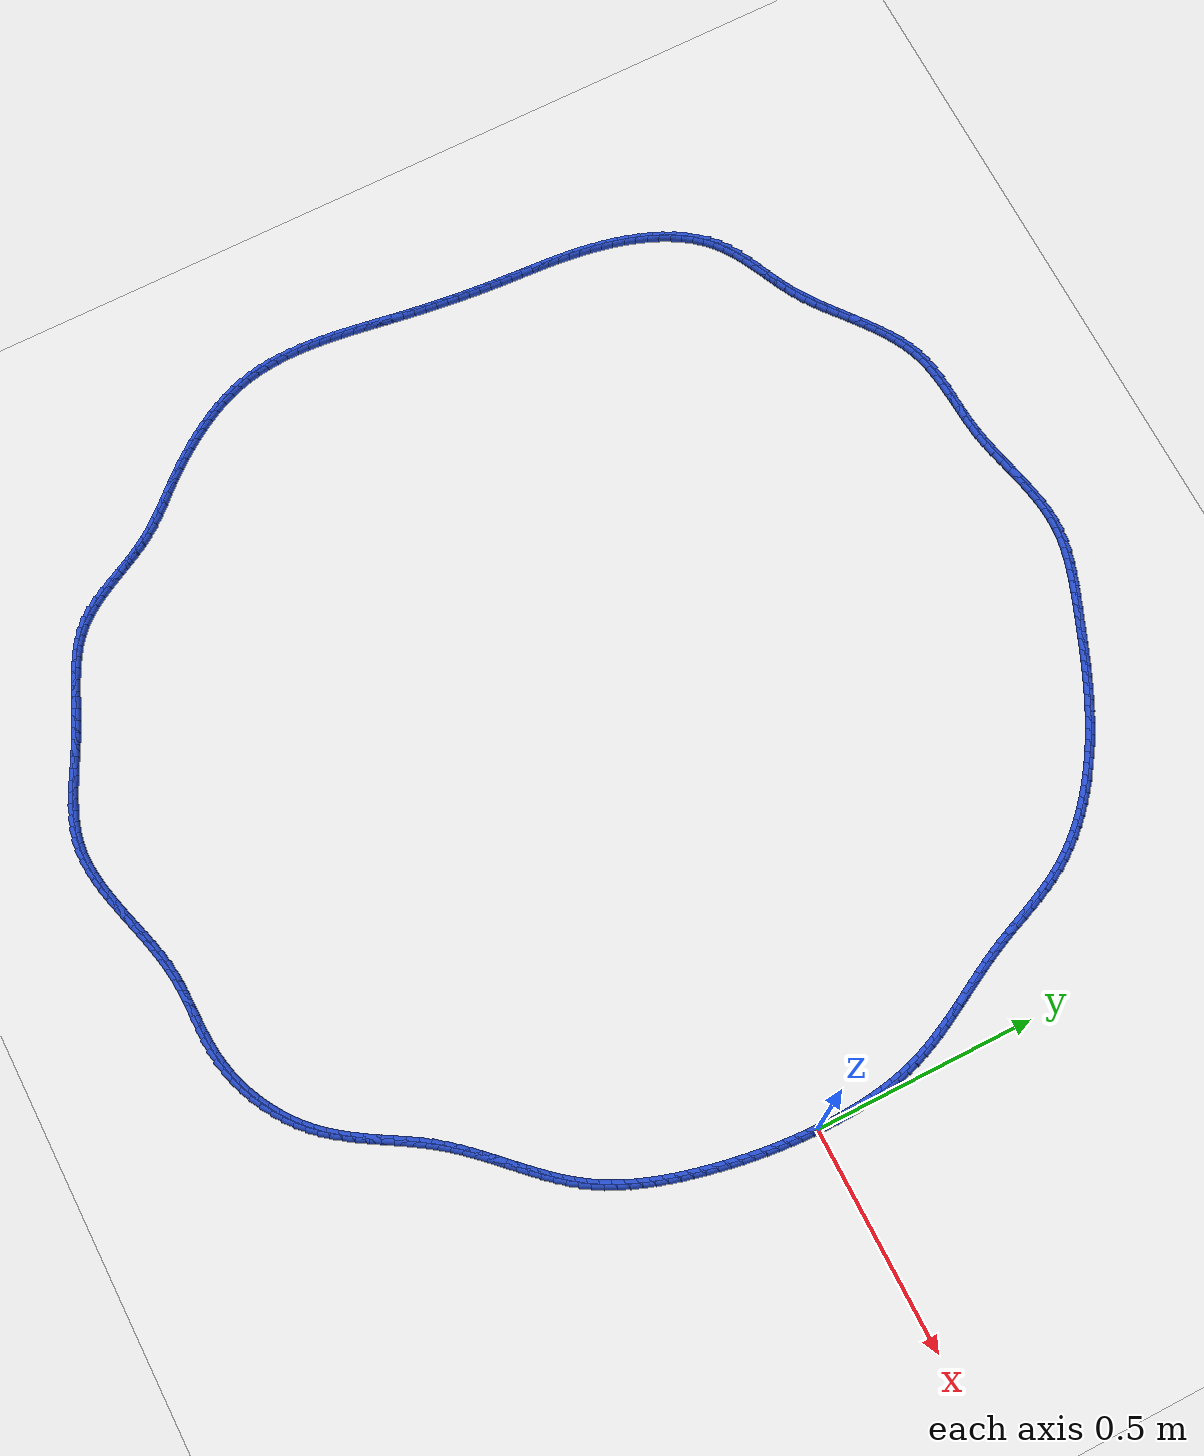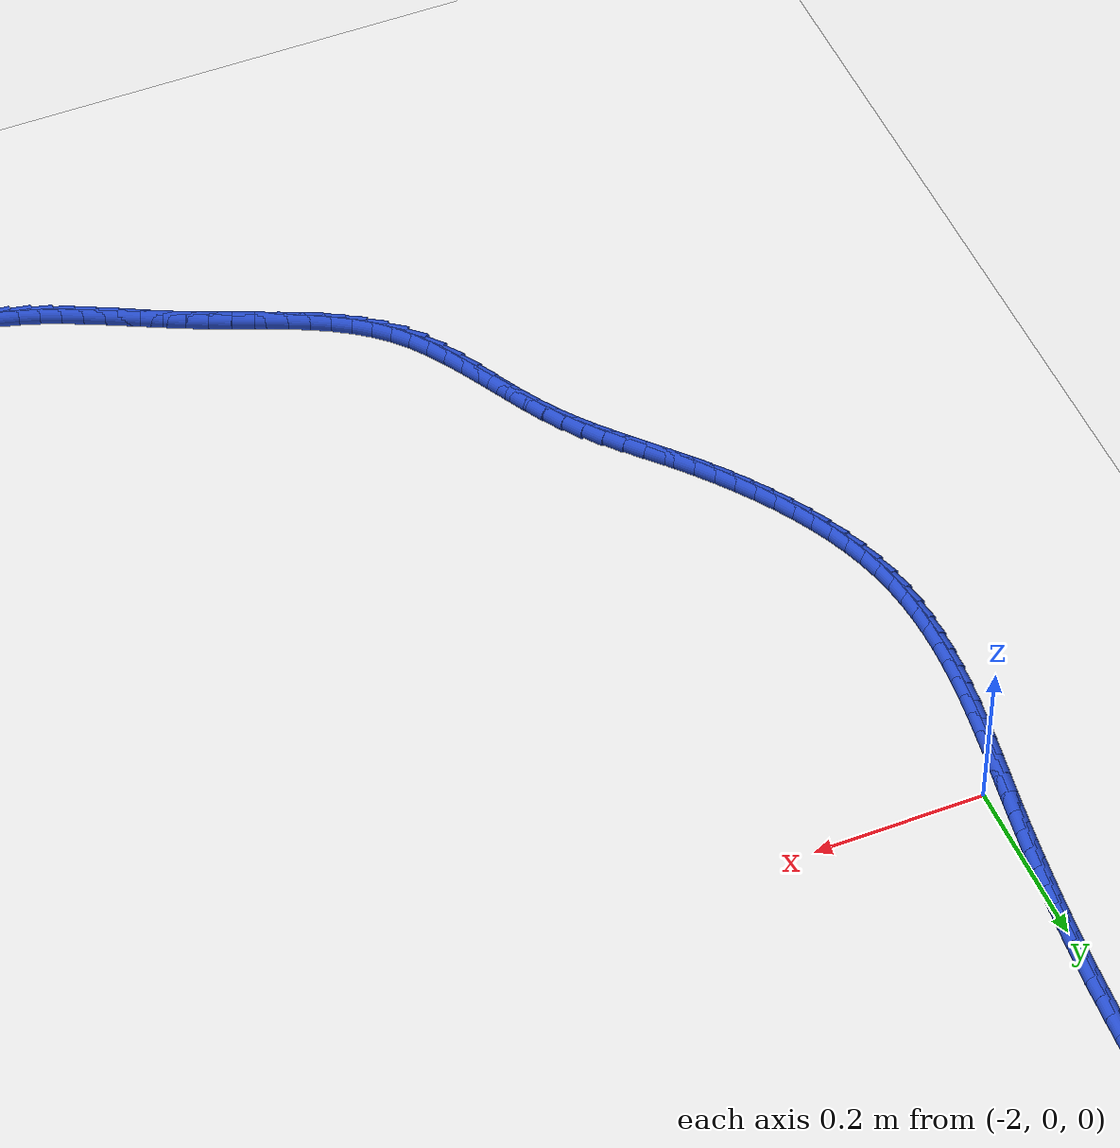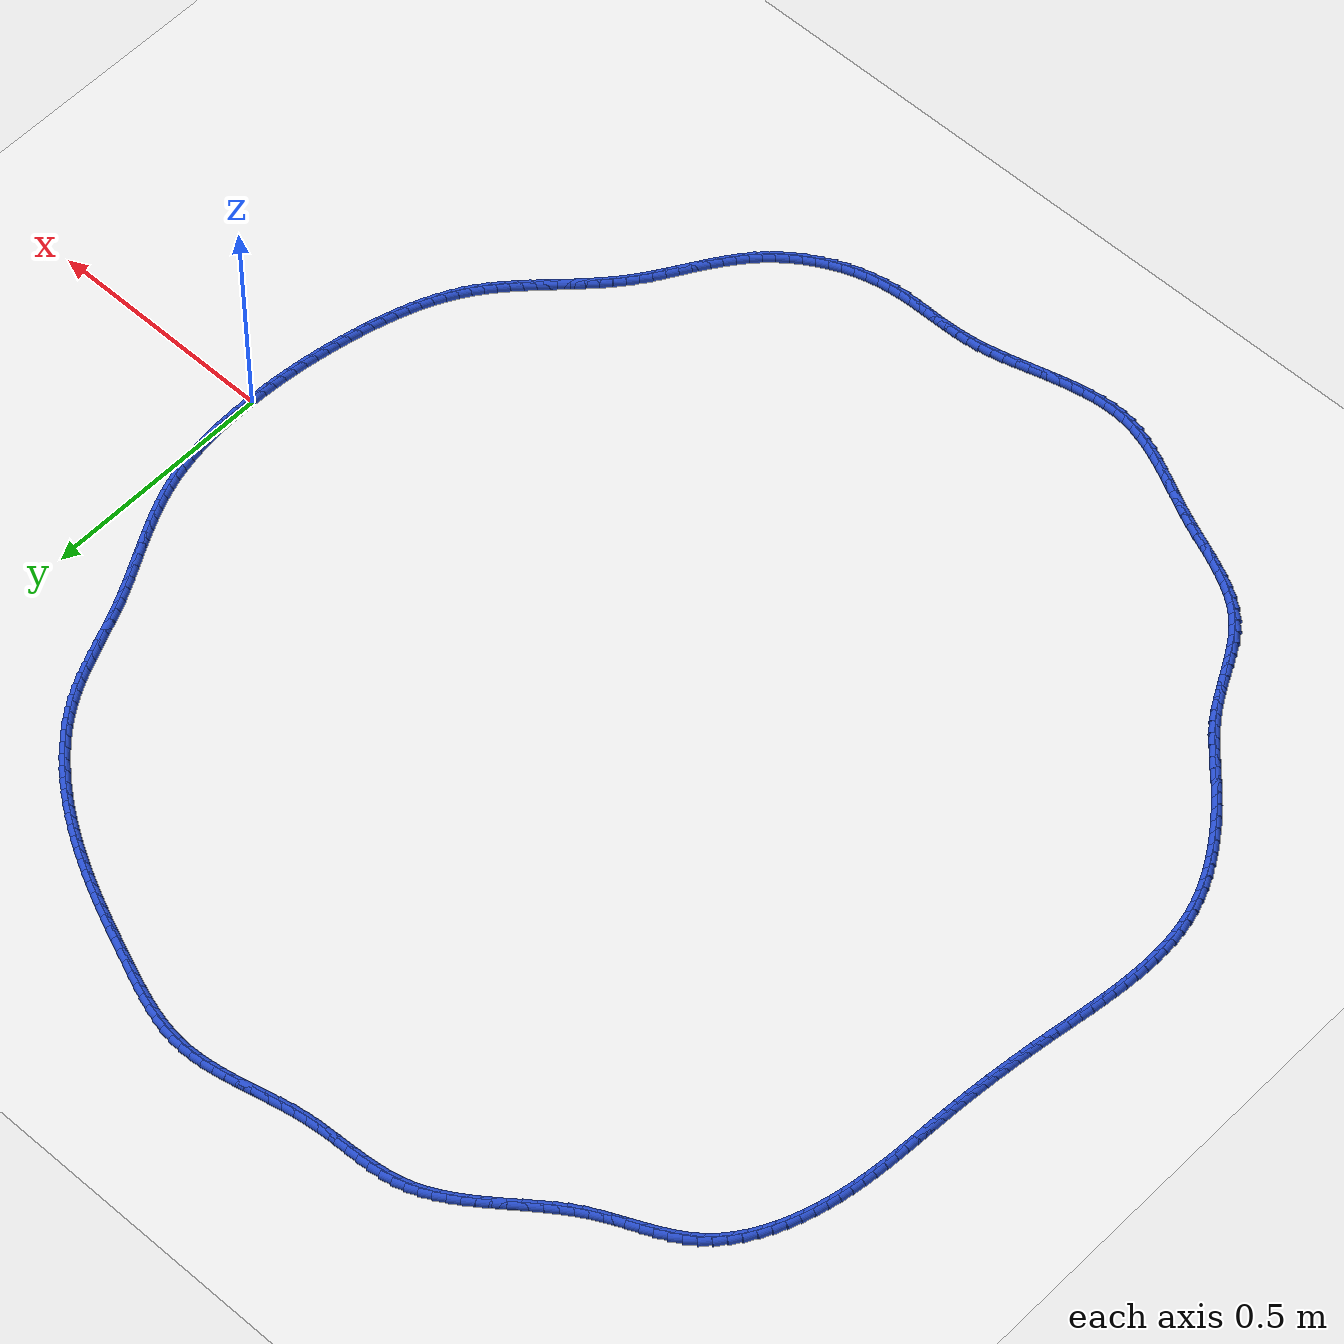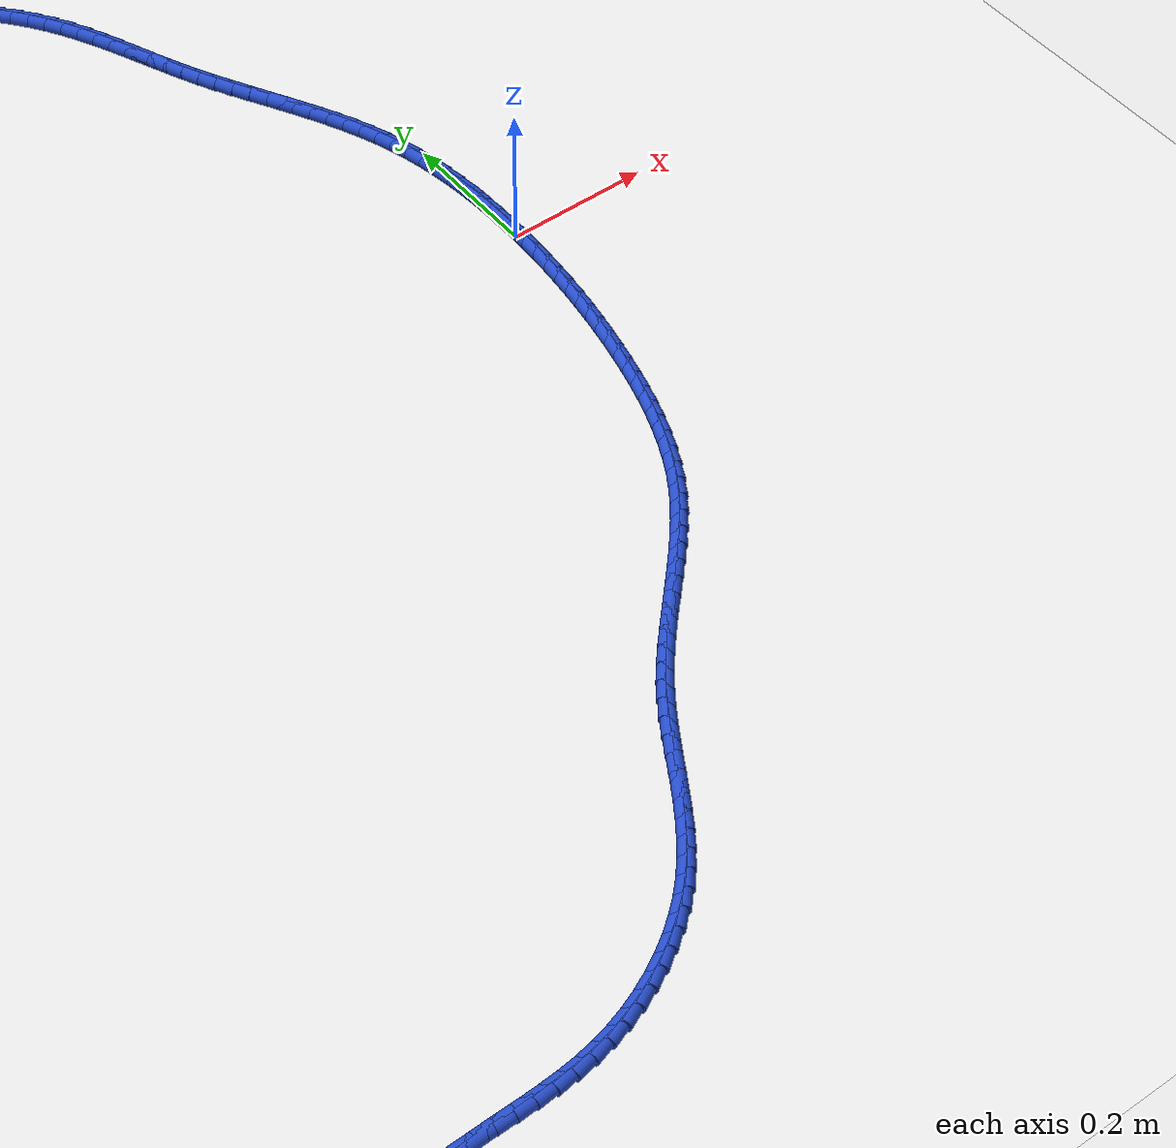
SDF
<sdf version="1.6">
 <world name="default">
  <light name="sun" type="directional">
   <pose>0 0 10 0 -0 0</pose>
   <diffuse>0.8 0.8 0.8 1</diffuse>
   <specular>0.2 0.2 0.2 1</specular>
   <attenuation>
    <range>1000</range>
    <constant>0.9</constant>
    <linear>0.01</linear>
    <quadratic>0.001</quadratic>
   </attenuation>
   <direction>-0.5 0.1 -0.9</direction>
  </light>
  <model name="ground_plane">
   <static>1</static>
   <link name="link">
    <collision name="collision">
     <geometry><plane><normal>0 0 1</normal><size>100 100</size></plane></geometry>
     <surface><friction><ode><mu>100</mu><mu2>50</mu2></ode></friction></surface>
    </collision>
    <visual name="visual">
     <cast_shadows>0</cast_shadows>
     <geometry><plane><normal>0 0 1</normal><size>100 100</size></plane></geometry>
     <material>
      <script><uri>file://media/materials/scripts/gazebo.material</uri><name>Gazebo/WhiteGlow</name></script>
     </material>
    </visual>
   </link>
  </model>
  <gravity>0 0 -9.8</gravity>
  <magnetic_field>6e-06 2.3e-05 -4.2e-05</magnetic_field>
  <atmosphere type="adiabatic"/>
  <physics name="default_physics" default="0" type="ode">
   <max_step_size>0.001</max_step_size>
   <real_time_factor>1</real_time_factor>
   <real_time_update_rate>1000</real_time_update_rate>
  </physics>
  <scene><ambient>0.4 0.4 0.4 1</ambient><background>0.7 0.7 0.7 1</background><shadows>1</shadows></scene>
  <spherical_coordinates>
   <surface_model>EARTH_WGS84</surface_model>
   <latitude_deg>0</latitude_deg>
   <longitude_deg>0</longitude_deg>
   <elevation>0</elevation>
   <heading_deg>0</heading_deg>
  </spherical_coordinates>
  <model name="line">
   <link name="link_0">
    <pose>-2.6020852139652106e-18 -5.551115123125783e-17 0.01 0 1.57 1.5606720008051456</pose>
    <collision name="collision">
     <geometry><cylinder><radius>0.01</radius><length>0.08</length></cylinder></geometry>
    </collision>
    <visual name="visual">
     <material>
      <script><name>Gazebo/Blue</name><uri>file://media/materials/scripts/gazebo.material</uri></script>
     </material>
     <geometry><cylinder><radius>0.01</radius><length>0.08</length></cylinder></geometry>
    </visual>
   </link>
   <link name="link_1">
    <pose>0.00026168912169531475 0.025846676675730935 0.01 0 1.57 -1.5566072044804915</pose>
    <collision name="collision">
     <geometry><cylinder><radius>0.01</radius><length>0.08</length></cylinder></geometry>
    </collision>
    <visual name="visual">
     <material>
      <script><name>Gazebo/Blue</name><uri>file://media/materials/scripts/gazebo.material</uri></script>
     </material>
     <geometry><cylinder><radius>0.01</radius><length>0.08</length></cylinder></geometry>
    </visual>
   </link>
   <link name="link_2">
    <pose>-0.00010585917153231922 0.05174846386459949 0.01 0 1.57 -1.5296821576817423</pose>
    <collision name="collision">
     <geometry><cylinder><radius>0.01</radius><length>0.08</length></cylinder></geometry>
    </collision>
    <visual name="visual">
     <material>
      <script><name>Gazebo/Blue</name><uri>file://media/materials/scripts/gazebo.material</uri></script>
     </material>
     <geometry><cylinder><radius>0.01</radius><length>0.08</length></cylinder></geometry>
    </visual>
   </link>
   <link name="link_3">
    <pose>-0.001171199643128076 0.07764562175381282 0.01 0 1.57 -1.5000092741032287</pose>
    <collision name="collision">
     <geometry><cylinder><radius>0.01</radius><length>0.08</length></cylinder></geometry>
    </collision>
    <visual name="visual">
     <material>
      <script><name>Gazebo/Blue</name><uri>file://media/materials/scripts/gazebo.material</uri></script>
     </material>
     <geometry><cylinder><radius>0.01</radius><length>0.08</length></cylinder></geometry>
    </visual>
   </link>
   <link name="link_4">
    <pose>-0.0030028870565371206 0.10347841053057813 0.01 0 1.57 -1.4674426135967553</pose>
    <collision name="collision">
     <geometry><cylinder><radius>0.01</radius><length>0.08</length></cylinder></geometry>
    </collision>
    <visual name="visual">
     <material>
      <script><name>Gazebo/Blue</name><uri>file://media/materials/scripts/gazebo.material</uri></script>
     </material>
     <geometry><cylinder><radius>0.01</radius><length>0.08</length></cylinder></geometry>
    </visual>
   </link>
   <link name="link_5">
    <pose>-0.005669476175204622 0.12918709038210263 0.01 0 1.57 -1.4318322130279397</pose>
    <collision name="collision">
     <geometry><cylinder><radius>0.01</radius><length>0.08</length></cylinder></geometry>
    </collision>
    <visual name="visual">
     <material>
      <script><name>Gazebo/Blue</name><uri>file://media/materials/scripts/gazebo.material</uri></script>
     </material>
     <geometry><cylinder><radius>0.01</radius><length>0.08</length></cylinder></geometry>
    </visual>
   </link>
   <link name="link_6">
    <pose>-0.009239521762575751 0.15471192149559365 0.01 0 1.57 -1.3930316349678902</pose>
    <collision name="collision">
     <geometry><cylinder><radius>0.01</radius><length>0.08</length></cylinder></geometry>
    </collision>
    <visual name="visual">
     <material>
      <script><name>Gazebo/Blue</name><uri>file://media/materials/scripts/gazebo.material</uri></script>
     </material>
     <geometry><cylinder><radius>0.01</radius><length>0.08</length></cylinder></geometry>
    </visual>
   </link>
   <link name="link_7">
    <pose>-0.013781578582095673 0.1799931640582583 0.01 0 1.57 -1.3509078144669298</pose>
    <collision name="collision">
     <geometry><cylinder><radius>0.01</radius><length>0.08</length></cylinder></geometry>
    </collision>
    <visual name="visual">
     <material>
      <script><name>Gazebo/Blue</name><uri>file://media/materials/scripts/gazebo.material</uri></script>
     </material>
     <geometry><cylinder><radius>0.01</radius><length>0.08</length></cylinder></geometry>
    </visual>
   </link>
   <link name="link_8">
    <pose>-0.019364201397209554 0.20497107825730382 0.01 0 1.57 -1.3053535194428476</pose>
    <collision name="collision">
     <geometry><cylinder><radius>0.01</radius><length>0.08</length></cylinder></geometry>
    </collision>
    <visual name="visual">
     <material>
      <script><name>Gazebo/Blue</name><uri>file://media/materials/scripts/gazebo.material</uri></script>
     </material>
     <geometry><cylinder><radius>0.01</radius><length>0.08</length></cylinder></geometry>
    </visual>
   </link>
   <link name="link_9">
    <pose>-0.02605594497136256 0.2295859242799375 0.01 0 1.57 -1.2566637800848937</pose>
    <collision name="collision">
     <geometry><cylinder><radius>0.01</radius><length>0.08</length></cylinder></geometry>
    </collision>
    <visual name="visual">
     <material>
      <script><name>Gazebo/Blue</name><uri>file://media/materials/scripts/gazebo.material</uri></script>
     </material>
     <geometry><cylinder><radius>0.01</radius><length>0.08</length></cylinder></geometry>
    </visual>
   </link>
   <link name="link_10">
    <pose>-0.033917150734529215 0.25378242759625824 0.01 0 1.57 -1.2102945592711332</pose>
    <collision name="collision">
     <geometry><cylinder><radius>0.01</radius><length>0.08</length></cylinder></geometry>
    </collision>
    <visual name="visual">
     <material>
      <script><name>Gazebo/Blue</name><uri>file://media/materials/scripts/gazebo.material</uri></script>
     </material>
     <geometry><cylinder><radius>0.01</radius><length>0.08</length></cylinder></geometry>
    </visual>
   </link>
   <link name="link_11">
    <pose>-0.042885287553008605 0.27757211490371175 0.01 0 1.57 -1.1706071240606626</pose>
    <collision name="collision">
     <geometry><cylinder><radius>0.01</radius><length>0.08</length></cylinder></geometry>
    </collision>
    <visual name="visual">
     <material>
      <script><name>Gazebo/Blue</name><uri>file://media/materials/scripts/gazebo.material</uri></script>
     </material>
     <geometry><cylinder><radius>0.01</radius><length>0.08</length></cylinder></geometry>
    </visual>
   </link>
   <link name="link_12">
    <pose>-0.05280324863534753 0.3010179301553623 0.01 0 1.57 -1.1378139994246075</pose>
    <collision name="collision">
     <geometry><cylinder><radius>0.01</radius><length>0.08</length></cylinder></geometry>
    </collision>
    <visual name="visual">
     <material>
      <script><name>Gazebo/Blue</name><uri>file://media/materials/scripts/gazebo.material</uri></script>
     </material>
     <geometry><cylinder><radius>0.01</radius><length>0.08</length></cylinder></geometry>
    </visual>
   </link>
   <link name="link_13">
    <pose>-0.06351149506214147 0.3241841395614755 0.01 0 1.57 -1.1119159873322897</pose>
    <collision name="collision">
     <geometry><cylinder><radius>0.01</radius><length>0.08</length></cylinder></geometry>
    </collision>
    <visual name="visual">
     <material>
      <script><name>Gazebo/Blue</name><uri>file://media/materials/scripts/gazebo.material</uri></script>
     </material>
     <geometry><cylinder><radius>0.01</radius><length>0.08</length></cylinder></geometry>
    </visual>
   </link>
   <link name="link_14">
    <pose>-0.07485048791398585 0.34713500933231717 0.01 0 1.57 -1.0928558864539948</pose>
    <collision name="collision">
     <geometry><cylinder><radius>0.01</radius><length>0.08</length></cylinder></geometry>
    </collision>
    <visual name="visual">
     <material>
      <script><name>Gazebo/Blue</name><uri>file://media/materials/scripts/gazebo.material</uri></script>
     </material>
     <geometry><cylinder><radius>0.01</radius><length>0.08</length></cylinder></geometry>
    </visual>
   </link>
   <link name="link_15">
    <pose>-0.08666068827147619 0.36993480567815323 0.01 0 1.57 -1.0805554052208224</pose>
    <collision name="collision">
     <geometry><cylinder><radius>0.01</radius><length>0.08</length></cylinder></geometry>
    </collision>
    <visual name="visual">
     <material>
      <script><name>Gazebo/Blue</name><uri>file://media/materials/scripts/gazebo.material</uri></script>
     </material>
     <geometry><cylinder><radius>0.01</radius><length>0.08</length></cylinder></geometry>
    </visual>
   </link>
   <link name="link_16">
    <pose>-0.09878255721520791 0.3926477948092493 0.01 0 1.57 -1.0749414477813892</pose>
    <collision name="collision">
     <geometry><cylinder><radius>0.01</radius><length>0.08</length></cylinder></geometry>
    </collision>
    <visual name="visual">
     <material>
      <script><name>Gazebo/Blue</name><uri>file://media/materials/scripts/gazebo.material</uri></script>
     </material>
     <geometry><cylinder><radius>0.01</radius><length>0.08</length></cylinder></geometry>
    </visual>
   </link>
   <link name="link_17">
    <pose>-0.11105655582577649 0.41533824293587124 0.01 0 1.57 -1.0759622935303972</pose>
    <collision name="collision">
     <geometry><cylinder><radius>0.01</radius><length>0.08</length></cylinder></geometry>
    </collision>
    <visual name="visual">
     <material>
      <script><name>Gazebo/Blue</name><uri>file://media/materials/scripts/gazebo.material</uri></script>
     </material>
     <geometry><cylinder><radius>0.01</radius><length>0.08</length></cylinder></geometry>
    </visual>
   </link>
   <link name="link_18">
    <pose>-0.12332314518377742 0.43807041626828486 0.01 0 1.57 -1.0835945328563317</pose>
    <collision name="collision">
     <geometry><cylinder><radius>0.01</radius><length>0.08</length></cylinder></geometry>
    </collision>
    <visual name="visual">
     <material>
      <script><name>Gazebo/Blue</name><uri>file://media/materials/scripts/gazebo.material</uri></script>
     </material>
     <geometry><cylinder><radius>0.01</radius><length>0.08</length></cylinder></geometry>
    </visual>
   </link>
   <link name="link_19">
    <pose>-0.13542278636980615 0.460908581016756 0.01 0 1.57 -1.0978413931100226</pose>
    <collision name="collision">
     <geometry><cylinder><radius>0.01</radius><length>0.08</length></cylinder></geometry>
    </collision>
    <visual name="visual">
     <material>
      <script><name>Gazebo/Blue</name><uri>file://media/materials/scripts/gazebo.material</uri></script>
     </material>
     <geometry><cylinder><radius>0.01</radius><length>0.08</length></cylinder></geometry>
    </visual>
   </link>
   <link name="link_20">
    <pose>-0.1471959404644581 0.4839170033915503 0.01 0 1.57 -1.1187226355027267</pose>
    <collision name="collision">
     <geometry><cylinder><radius>0.01</radius><length>0.08</length></cylinder></geometry>
    </collision>
    <visual name="visual">
     <material>
      <script><name>Gazebo/Blue</name><uri>file://media/materials/scripts/gazebo.material</uri></script>
     </material>
     <geometry><cylinder><radius>0.01</radius><length>0.08</length></cylinder></geometry>
    </visual>
   </link>
   <link name="link_21">
    <pose>-0.1584830685483288 0.5071599496029338 0.01 0 1.57 -1.1443971395748282</pose>
    <collision name="collision">
     <geometry><cylinder><radius>0.01</radius><length>0.08</length></cylinder></geometry>
    </collision>
    <visual name="visual">
     <material>
      <script><name>Gazebo/Blue</name><uri>file://media/materials/scripts/gazebo.material</uri></script>
     </material>
     <geometry><cylinder><radius>0.01</radius><length>0.08</length></cylinder></geometry>
    </visual>
   </link>
   <link name="link_22">
    <pose>-0.16916794045748912 0.530680921171539 0.01 0 1.57 -1.1641771697265613</pose>
    <collision name="collision">
     <geometry><cylinder><radius>0.01</radius><length>0.08</length></cylinder></geometry>
    </collision>
    <visual name="visual">
     <material>
      <script><name>Gazebo/Blue</name><uri>file://media/materials/scripts/gazebo.material</uri></script>
     </material>
     <geometry><cylinder><radius>0.01</radius><length>0.08</length></cylinder></geometry>
    </visual>
   </link>
   <link name="link_23">
    <pose>-0.17938349545723303 0.5544039535699202 0.01 0 1.57 -1.1742620330604225</pose>
    <collision name="collision">
     <geometry><cylinder><radius>0.01</radius><length>0.08</length></cylinder></geometry>
    </collision>
    <visual name="visual">
     <material>
      <script><name>Gazebo/Blue</name><uri>file://media/materials/scripts/gazebo.material</uri></script>
     </material>
     <geometry><cylinder><radius>0.01</radius><length>0.08</length></cylinder></geometry>
    </visual>
   </link>
   <link name="link_24">
    <pose>-0.18935160505198612 0.5782104430785403 0.01 0 1.57 -1.1746459700017604</pose>
    <collision name="collision">
     <geometry><cylinder><radius>0.01</radius><length>0.08</length></cylinder></geometry>
    </collision>
    <visual name="visual">
     <material>
      <script><name>Gazebo/Blue</name><uri>file://media/materials/scripts/gazebo.material</uri></script>
     </material>
     <geometry><cylinder><radius>0.01</radius><length>0.08</length></cylinder></geometry>
    </visual>
   </link>
   <link name="link_25">
    <pose>-0.19929425106854684 0.6019817330830197 0.01 0 1.57 -1.165282038848789</pose>
    <collision name="collision">
     <geometry><cylinder><radius>0.01</radius><length>0.08</length></cylinder></geometry>
    </collision>
    <visual name="visual">
     <material>
      <script><name>Gazebo/Blue</name><uri>file://media/materials/scripts/gazebo.material</uri></script>
     </material>
     <geometry><cylinder><radius>0.01</radius><length>0.08</length></cylinder></geometry>
    </visual>
   </link>
   <link name="link_26">
    <pose>-0.2094334153337134 0.6255991669689782 0.01 0 1.57 -1.1460755867648575</pose>
    <collision name="collision">
     <geometry><cylinder><radius>0.01</radius><length>0.08</length></cylinder></geometry>
    </collision>
    <visual name="visual">
     <material>
      <script><name>Gazebo/Blue</name><uri>file://media/materials/scripts/gazebo.material</uri></script>
     </material>
     <geometry><cylinder><radius>0.01</radius><length>0.08</length></cylinder></geometry>
    </visual>
   </link>
   <link name="link_27">
    <pose>-0.2199910796742838 0.6489440881220354 0.01 0 1.57 -1.116910302068992</pose>
    <collision name="collision">
     <geometry><cylinder><radius>0.01</radius><length>0.08</length></cylinder></geometry>
    </collision>
    <visual name="visual">
     <material>
      <script><name>Gazebo/Blue</name><uri>file://media/materials/scripts/gazebo.material</uri></script>
     </material>
     <geometry><cylinder><radius>0.01</radius><length>0.08</length></cylinder></geometry>
    </visual>
   </link>
   <link name="link_28">
    <pose>-0.23118922591705668 0.6718978399278123 0.01 0 1.57 -1.0777043868660467</pose>
    <collision name="collision">
     <geometry><cylinder><radius>0.01</radius><length>0.08</length></cylinder></geometry>
    </collision>
    <visual name="visual">
     <material>
      <script><name>Gazebo/Blue</name><uri>file://media/materials/scripts/gazebo.material</uri></script>
     </material>
     <geometry><cylinder><radius>0.01</radius><length>0.08</length></cylinder></geometry>
    </visual>
   </link>
   <link name="link_29">
    <pose>-0.2432498358888298 0.6943417657719279 0.01 0 1.57 -1.0285021204887723</pose>
    <collision name="collision">
     <geometry><cylinder><radius>0.01</radius><length>0.08</length></cylinder></geometry>
    </collision>
    <visual name="visual">
     <material>
      <script><name>Gazebo/Blue</name><uri>file://media/materials/scripts/gazebo.material</uri></script>
     </material>
     <geometry><cylinder><radius>0.01</radius><length>0.08</length></cylinder></geometry>
    </visual>
   </link>
   <link name="link_30">
    <pose>-0.2563948047004046 0.7161572413904448 0.01 0 1.57 -0.9726038961689899</pose>
    <collision name="collision">
     <geometry><cylinder><radius>0.01</radius><length>0.08</length></cylinder></geometry>
    </collision>
    <visual name="visual">
     <material>
      <script><name>Gazebo/Blue</name><uri>file://media/materials/scripts/gazebo.material</uri></script>
     </material>
     <geometry><cylinder><radius>0.01</radius><length>0.08</length></cylinder></geometry>
    </visual>
   </link>
   <link name="link_31">
    <pose>-0.27077156626795024 0.7372534211603304 0.01 0 1.57 -0.9187925252951772</pose>
    <collision name="collision">
     <geometry><cylinder><radius>0.01</radius><length>0.08</length></cylinder></geometry>
    </collision>
    <visual name="visual">
     <material>
      <script><name>Gazebo/Blue</name><uri>file://media/materials/scripts/gazebo.material</uri></script>
     </material>
     <geometry><cylinder><radius>0.01</radius><length>0.08</length></cylinder></geometry>
    </visual>
   </link>
   <link name="link_32">
    <pose>-0.2863172360465632 0.7576179212806456 0.01 0 1.57 -0.868501504472318</pose>
    <collision name="collision">
     <geometry><cylinder><radius>0.01</radius><length>0.08</length></cylinder></geometry>
    </collision>
    <visual name="visual">
     <material>
      <script><name>Gazebo/Blue</name><uri>file://media/materials/scripts/gazebo.material</uri></script>
     </material>
     <geometry><cylinder><radius>0.01</radius><length>0.08</length></cylinder></geometry>
    </visual>
   </link>
   <link name="link_33">
    <pose>-0.30293205936250106 0.7772521127938193 0.01 0 1.57 -0.821585448601514</pose>
    <collision name="collision">
     <geometry><cylinder><radius>0.01</radius><length>0.08</length></cylinder></geometry>
    </collision>
    <visual name="visual">
     <material>
      <script><name>Gazebo/Blue</name><uri>file://media/materials/scripts/gazebo.material</uri></script>
     </material>
     <geometry><cylinder><radius>0.01</radius><length>0.08</length></cylinder></geometry>
    </visual>
   </link>
   <link name="link_34">
    <pose>-0.32051628154202194 0.7961573667422805 0.01 0 1.57 -0.7778589333654485</pose>
    <collision name="collision">
     <geometry><cylinder><radius>0.01</radius><length>0.08</length></cylinder></geometry>
    </collision>
    <visual name="visual">
     <material>
      <script><name>Gazebo/Blue</name><uri>file://media/materials/scripts/gazebo.material</uri></script>
     </material>
     <geometry><cylinder><radius>0.01</radius><length>0.08</length></cylinder></geometry>
    </visual>
   </link>
   <link name="link_35">
    <pose>-0.3389701479113833 0.8143350541684585 0.01 0 1.57 -0.7371125624628163</pose>
    <collision name="collision">
     <geometry><cylinder><radius>0.01</radius><length>0.08</length></cylinder></geometry>
    </collision>
    <visual name="visual">
     <material>
      <script><name>Gazebo/Blue</name><uri>file://media/materials/scripts/gazebo.material</uri></script>
     </material>
     <geometry><cylinder><radius>0.01</radius><length>0.08</length></cylinder></geometry>
    </visual>
   </link>
   <link name="link_36">
    <pose>-0.35819390379684296 0.8317865461147819 0.01 0 1.57 -0.6991252725397453</pose>
    <collision name="collision">
     <geometry><cylinder><radius>0.01</radius><length>0.08</length></cylinder></geometry>
    </collision>
    <visual name="visual">
     <material>
      <script><name>Gazebo/Blue</name><uri>file://media/materials/scripts/gazebo.material</uri></script>
     </material>
     <geometry><cylinder><radius>0.01</radius><length>0.08</length></cylinder></geometry>
    </visual>
   </link>
   <link name="link_37">
    <pose>-0.37808779452465857 0.8485132136236796 0.01 0 1.57 -0.6636732380263552</pose>
    <collision name="collision">
     <geometry><cylinder><radius>0.01</radius><length>0.08</length></cylinder></geometry>
    </collision>
    <visual name="visual">
     <material>
      <script><name>Gazebo/Blue</name><uri>file://media/materials/scripts/gazebo.material</uri></script>
     </material>
     <geometry><cylinder><radius>0.01</radius><length>0.08</length></cylinder></geometry>
    </visual>
   </link>
   <link name="link_38">
    <pose>-0.39855206542108823 0.8645164277375813 0.01 0 1.57 -0.6305359186612792</pose>
    <collision name="collision">
     <geometry><cylinder><radius>0.01</radius><length>0.08</length></cylinder></geometry>
    </collision>
    <visual name="visual">
     <material>
      <script><name>Gazebo/Blue</name><uri>file://media/materials/scripts/gazebo.material</uri></script>
     </material>
     <geometry><cylinder><radius>0.01</radius><length>0.08</length></cylinder></geometry>
    </visual>
   </link>
   <link name="link_39">
    <pose>-0.4194869618123894 0.8797975594989151 0.01 0 1.57 -0.5994976577316703</pose>
    <collision name="collision">
     <geometry><cylinder><radius>0.01</radius><length>0.08</length></cylinder></geometry>
    </collision>
    <visual name="visual">
     <material>
      <script><name>Gazebo/Blue</name><uri>file://media/materials/scripts/gazebo.material</uri></script>
     </material>
     <geometry><cylinder><radius>0.01</radius><length>0.08</length></cylinder></geometry>
    </visual>
   </link>
   <link name="link_40">
    <pose>-0.4407936989977522 0.8943585752006334 0.01 0 1.57 -0.5703247286395975</pose>
    <collision name="collision">
     <geometry><cylinder><radius>0.01</radius><length>0.08</length></cylinder></geometry>
    </collision>
    <visual name="visual">
     <material>
      <script><name>Gazebo/Blue</name><uri>file://media/materials/scripts/gazebo.material</uri></script>
     </material>
     <geometry><cylinder><radius>0.01</radius><length>0.08</length></cylinder></geometry>
    </visual>
   </link>
   <link name="link_41">
    <pose>-0.4624098339774462 0.9082237432184129 0.01 0 1.57 -0.5429785711575642</pose>
    <collision name="collision">
     <geometry><cylinder><radius>0.01</radius><length>0.08</length></cylinder></geometry>
    </collision>
    <visual name="visual">
     <material>
      <script><name>Gazebo/Blue</name><uri>file://media/materials/scripts/gazebo.material</uri></script>
     </material>
     <geometry><cylinder><radius>0.01</radius><length>0.08</length></cylinder></geometry>
    </visual>
   </link>
   <link name="link_42">
    <pose>-0.4843193575159778 0.9214458272823145 0.01 0 1.57 -0.517570465941171</pose>
    <collision name="collision">
     <geometry><cylinder><radius>0.01</radius><length>0.08</length></cylinder></geometry>
    </collision>
    <visual name="visual">
     <material>
      <script><name>Gazebo/Blue</name><uri>file://media/materials/scripts/gazebo.material</uri></script>
     </material>
     <geometry><cylinder><radius>0.01</radius><length>0.08</length></cylinder></geometry>
    </visual>
   </link>
   <link name="link_43">
    <pose>-0.5065092868379267 0.9340794483927238 0.01 0 1.57 -0.4941953560387322</pose>
    <collision name="collision">
     <geometry><cylinder><radius>0.01</radius><length>0.08</length></cylinder></geometry>
    </collision>
    <visual name="visual">
     <material>
      <script><name>Gazebo/Blue</name><uri>file://media/materials/scripts/gazebo.material</uri></script>
     </material>
     <geometry><cylinder><radius>0.01</radius><length>0.08</length></cylinder></geometry>
    </visual>
   </link>
   <link name="link_44">
    <pose>-0.5289666391678735 0.9461792275500257 0.01 0 1.57 -0.47292653974310134</pose>
    <collision name="collision">
     <geometry><cylinder><radius>0.01</radius><length>0.08</length></cylinder></geometry>
    </collision>
    <visual name="visual">
     <material>
      <script><name>Gazebo/Blue</name><uri>file://media/materials/scripts/gazebo.material</uri></script>
     </material>
     <geometry><cylinder><radius>0.01</radius><length>0.08</length></cylinder></geometry>
    </visual>
   </link>
   <link name="link_45">
    <pose>-0.5516784317303979 0.9577997857546059 0.01 0 1.57 -0.45381763930004954</pose>
    <collision name="collision">
     <geometry><cylinder><radius>0.01</radius><length>0.08</length></cylinder></geometry>
    </collision>
    <visual name="visual">
     <material>
      <script><name>Gazebo/Blue</name><uri>file://media/materials/scripts/gazebo.material</uri></script>
     </material>
     <geometry><cylinder><radius>0.01</radius><length>0.08</length></cylinder></geometry>
    </visual>
   </link>
   <link name="link_46">
    <pose>-0.5746316817500805 0.9689957440068487 0.01 0 1.57 -0.436904879874559</pose>
    <collision name="collision">
     <geometry><cylinder><radius>0.01</radius><length>0.08</length></cylinder></geometry>
    </collision>
    <visual name="visual">
     <material>
      <script><name>Gazebo/Blue</name><uri>file://media/materials/scripts/gazebo.material</uri></script>
     </material>
     <geometry><cylinder><radius>0.01</radius><length>0.08</length></cylinder></geometry>
    </visual>
   </link>
   <link name="link_47">
    <pose>-0.5978134064515013 0.9798217233071401 0.01 0 1.57 -0.42220948752634563</pose>
    <collision name="collision">
     <geometry><cylinder><radius>0.01</radius><length>0.08</length></cylinder></geometry>
    </collision>
    <visual name="visual">
     <material>
      <script><name>Gazebo/Blue</name><uri>file://media/materials/scripts/gazebo.material</uri></script>
     </material>
     <geometry><cylinder><radius>0.01</radius><length>0.08</length></cylinder></geometry>
    </visual>
   </link>
   <link name="link_48">
    <pose>-0.6212106230592401 0.9903323446558651 0.01 0 1.57 -0.4097400491713788</pose>
    <collision name="collision">
     <geometry><cylinder><radius>0.01</radius><length>0.08</length></cylinder></geometry>
    </collision>
    <visual name="visual">
     <material>
      <script><name>Gazebo/Blue</name><uri>file://media/materials/scripts/gazebo.material</uri></script>
     </material>
     <geometry><cylinder><radius>0.01</radius><length>0.08</length></cylinder></geometry>
    </visual>
   </link>
   <link name="link_49">
    <pose>-0.6448103487978774 1.0005822290534085 0.01 0 1.57 -0.39949471489185256</pose>
    <collision name="collision">
     <geometry><cylinder><radius>0.01</radius><length>0.08</length></cylinder></geometry>
    </collision>
    <visual name="visual">
     <material>
      <script><name>Gazebo/Blue</name><uri>file://media/materials/scripts/gazebo.material</uri></script>
     </material>
     <geometry><cylinder><radius>0.01</radius><length>0.08</length></cylinder></geometry>
    </visual>
   </link>
   <link name="link_50">
    <pose>-0.6685996008919932 1.010625997500156 0.01 0 1.57 -0.3914631587835882</pose>
    <collision name="collision">
     <geometry><cylinder><radius>0.01</radius><length>0.08</length></cylinder></geometry>
    </collision>
    <visual name="visual">
     <material>
      <script><name>Gazebo/Blue</name><uri>file://media/materials/scripts/gazebo.material</uri></script>
     </material>
     <geometry><cylinder><radius>0.01</radius><length>0.08</length></cylinder></geometry>
    </visual>
   </link>
   <link name="link_51">
    <pose>-0.6925653965661681 1.0205182709964924 0.01 0 1.57 -0.3856282459099491</pose>
    <collision name="collision">
     <geometry><cylinder><radius>0.01</radius><length>0.08</length></cylinder></geometry>
    </collision>
    <visual name="visual">
     <material>
      <script><name>Gazebo/Blue</name><uri>file://media/materials/scripts/gazebo.material</uri></script>
     </material>
     <geometry><cylinder><radius>0.01</radius><length>0.08</length></cylinder></geometry>
    </visual>
   </link>
   <link name="link_52">
    <pose>-0.7166947530449813 1.030313670542803 0.01 0 1.57 -0.381757426390218</pose>
    <collision name="collision">
     <geometry><cylinder><radius>0.01</radius><length>0.08</length></cylinder></geometry>
    </collision>
    <visual name="visual">
     <material>
      <script><name>Gazebo/Blue</name><uri>file://media/materials/scripts/gazebo.material</uri></script>
     </material>
     <geometry><cylinder><radius>0.01</radius><length>0.08</length></cylinder></geometry>
    </visual>
   </link>
   <link name="link_53">
    <pose>-0.7409746263709259 1.0400608729017524 0.01 0 1.57 -0.37437469125563466</pose>
    <collision name="collision">
     <geometry><cylinder><radius>0.01</radius><length>0.08</length></cylinder></geometry>
    </collision>
    <visual name="visual">
     <material>
      <script><name>Gazebo/Blue</name><uri>file://media/materials/scripts/gazebo.material</uri></script>
     </material>
     <geometry><cylinder><radius>0.01</radius><length>0.08</length></cylinder></geometry>
    </visual>
   </link>
   <link name="link_54">
    <pose>-0.7653903811274507 1.049653934239682 0.01 0 1.57 -0.3575897353035585</pose>
    <collision name="collision">
     <geometry><cylinder><radius>0.01</radius><length>0.08</length></cylinder></geometry>
    </collision>
    <visual name="visual">
     <material>
      <script><name>Gazebo/Blue</name><uri>file://media/materials/scripts/gazebo.material</uri></script>
     </material>
     <geometry><cylinder><radius>0.01</radius><length>0.08</length></cylinder></geometry>
    </visual>
   </link>
   <link name="link_55">
    <pose>-0.7899256807906675 1.058821637081913 0.01 0 1.57 -0.3308634066605244</pose>
    <collision name="collision">
     <geometry><cylinder><radius>0.01</radius><length>0.08</length></cylinder></geometry>
    </collision>
    <visual name="visual">
     <material>
      <script><name>Gazebo/Blue</name><uri>file://media/materials/scripts/gazebo.material</uri></script>
     </material>
     <geometry><cylinder><radius>0.01</radius><length>0.08</length></cylinder></geometry>
    </visual>
   </link>
   <link name="link_56">
    <pose>-0.8145641056944198 1.06728468614163 0.01 0 1.57 -0.2937394545139934</pose>
    <collision name="collision">
     <geometry><cylinder><radius>0.01</radius><length>0.08</length></cylinder></geometry>
    </collision>
    <visual name="visual">
     <material>
      <script><name>Gazebo/Blue</name><uri>file://media/materials/scripts/gazebo.material</uri></script>
     </material>
     <geometry><cylinder><radius>0.01</radius><length>0.08</length></cylinder></geometry>
    </visual>
   </link>
   <link name="link_57">
    <pose>-0.8392892361725509 1.0747637861320178 0.01 0 1.57 -0.24562389785741015</pose>
    <collision name="collision">
     <geometry><cylinder><radius>0.01</radius><length>0.08</length></cylinder></geometry>
    </collision>
    <visual name="visual">
     <material>
      <script><name>Gazebo/Blue</name><uri>file://media/materials/scripts/gazebo.material</uri></script>
     </material>
     <geometry><cylinder><radius>0.01</radius><length>0.08</length></cylinder></geometry>
    </visual>
   </link>
   <link name="link_58">
    <pose>-0.8640846525589053 1.0809796417662605 0.01 0 1.57 -0.18589509119703854</pose>
    <collision name="collision">
     <geometry><cylinder><radius>0.01</radius><length>0.08</length></cylinder></geometry>
    </collision>
    <visual name="visual">
     <material>
      <script><name>Gazebo/Blue</name><uri>file://media/materials/scripts/gazebo.material</uri></script>
     </material>
     <geometry><cylinder><radius>0.01</radius><length>0.08</length></cylinder></geometry>
    </visual>
   </link>
   <link name="link_59">
    <pose>-0.8889339351873253 1.0856529577575422 0.01 0 1.57 -0.11408088787265616</pose>
    <collision name="collision">
     <geometry><cylinder><radius>0.01</radius><length>0.08</length></cylinder></geometry>
    </collision>
    <visual name="visual">
     <material>
      <script><name>Gazebo/Blue</name><uri>file://media/materials/scripts/gazebo.material</uri></script>
     </material>
     <geometry><cylinder><radius>0.01</radius><length>0.08</length></cylinder></geometry>
    </visual>
   </link>
   <link name="link_60">
    <pose>-0.9138206643916549 1.088504438819048 0.01 0 1.57 -0.03259964631753431</pose>
    <collision name="collision">
     <geometry><cylinder><radius>0.01</radius><length>0.08</length></cylinder></geometry>
    </collision>
    <visual name="visual">
     <material>
      <script><name>Gazebo/Blue</name><uri>file://media/materials/scripts/gazebo.material</uri></script>
     </material>
     <geometry><cylinder><radius>0.01</radius><length>0.08</length></cylinder></geometry>
    </visual>
   </link>
   <link name="link_61">
    <pose>-0.9387318740127207 1.0893168232460746 0.01 0 1.57 0.04255443384385552</pose>
    <collision name="collision">
     <geometry><cylinder><radius>0.01</radius><length>0.08</length></cylinder></geometry>
    </collision>
    <visual name="visual">
     <material>
      <script><name>Gazebo/Blue</name><uri>file://media/materials/scripts/gazebo.material</uri></script>
     </material>
     <geometry><cylinder><radius>0.01</radius><length>0.08</length></cylinder></geometry>
    </visual>
   </link>
   <link name="link_62">
    <pose>-0.9636758563961211 1.0882547049976836 0.01 0 1.57 0.10471824326895153</pose>
    <collision name="collision">
     <geometry><cylinder><radius>0.01</radius><length>0.08</length></cylinder></geometry>
    </collision>
    <visual name="visual">
     <material>
      <script><name>Gazebo/Blue</name><uri>file://media/materials/scripts/gazebo.material</uri></script>
     </material>
     <geometry><cylinder><radius>0.01</radius><length>0.08</length></cylinder></geometry>
    </visual>
   </link>
   <link name="link_63">
    <pose>-0.9886689863616577 1.0856278593890523 0.01 0 1.57 0.15367585824851632</pose>
    <collision name="collision">
     <geometry><cylinder><radius>0.01</radius><length>0.08</length></cylinder></geometry>
    </collision>
    <visual name="visual">
     <material>
      <script><name>Gazebo/Blue</name><uri>file://media/materials/scripts/gazebo.material</uri></script>
     </material>
     <geometry><cylinder><radius>0.01</radius><length>0.08</length></cylinder></geometry>
    </visual>
   </link>
   <link name="link_64">
    <pose>-1.0137276543993818 1.0817463432120618 0.01 0 1.57 0.18965838416106814</pose>
    <collision name="collision">
     <geometry><cylinder><radius>0.01</radius><length>0.08</length></cylinder></geometry>
    </collision>
    <visual name="visual">
     <material>
      <script><name>Gazebo/Blue</name><uri>file://media/materials/scripts/gazebo.material</uri></script>
     </material>
     <geometry><cylinder><radius>0.01</radius><length>0.08</length></cylinder></geometry>
    </visual>
   </link>
   <link name="link_65">
    <pose>-1.0388682509993457 1.0769202132585929 0.01 0 1.57 0.21307552401293783</pose>
    <collision name="collision">
     <geometry><cylinder><radius>0.01</radius><length>0.08</length></cylinder></geometry>
    </collision>
    <visual name="visual">
     <material>
      <script><name>Gazebo/Blue</name><uri>file://media/materials/scripts/gazebo.material</uri></script>
     </material>
     <geometry><cylinder><radius>0.01</radius><length>0.08</length></cylinder></geometry>
    </visual>
   </link>
   <link name="link_66">
    <pose>-1.0641071666516015 1.0714595263205273 0.01 0 1.57 0.22433902805660094</pose>
    <collision name="collision">
     <geometry><cylinder><radius>0.01</radius><length>0.08</length></cylinder></geometry>
    </collision>
    <visual name="visual">
     <material>
      <script><name>Gazebo/Blue</name><uri>file://media/materials/scripts/gazebo.material</uri></script>
     </material>
     <geometry><cylinder><radius>0.01</radius><length>0.08</length></cylinder></geometry>
    </visual>
   </link>
   <link name="link_67">
    <pose>-1.089460791846201 1.0656743391897456 0.01 0 1.57 0.22376192650550664</pose>
    <collision name="collision">
     <geometry><cylinder><radius>0.01</radius><length>0.08</length></cylinder></geometry>
    </collision>
    <visual name="visual">
     <material>
      <script><name>Gazebo/Blue</name><uri>file://media/materials/scripts/gazebo.material</uri></script>
     </material>
     <geometry><cylinder><radius>0.01</radius><length>0.08</length></cylinder></geometry>
    </visual>
   </link>
   <link name="link_68">
    <pose>-1.1149455170731952 1.0598747086581295 0.01 0 1.57 0.211518502137762</pose>
    <collision name="collision">
     <geometry><cylinder><radius>0.01</radius><length>0.08</length></cylinder></geometry>
    </collision>
    <visual name="visual">
     <material>
      <script><name>Gazebo/Blue</name><uri>file://media/materials/scripts/gazebo.material</uri></script>
     </material>
     <geometry><cylinder><radius>0.01</radius><length>0.08</length></cylinder></geometry>
    </visual>
   </link>
   <link name="link_69">
    <pose>-1.1405777328226372 1.0543706915175606 0.01 0 1.57 0.18765301356978514</pose>
    <collision name="collision">
     <geometry><cylinder><radius>0.01</radius><length>0.08</length></cylinder></geometry>
    </collision>
    <visual name="visual">
     <material>
      <script><name>Gazebo/Blue</name><uri>file://media/materials/scripts/gazebo.material</uri></script>
     </material>
     <geometry><cylinder><radius>0.01</radius><length>0.08</length></cylinder></geometry>
    </visual>
   </link>
   <link name="link_70">
    <pose>-1.166373829584579 1.0494723445599194 0.01 0 1.57 0.15213241074228684</pose>
    <collision name="collision">
     <geometry><cylinder><radius>0.01</radius><length>0.08</length></cylinder></geometry>
    </collision>
    <visual name="visual">
     <material>
      <script><name>Gazebo/Blue</name><uri>file://media/materials/scripts/gazebo.material</uri></script>
     </material>
     <geometry><cylinder><radius>0.01</radius><length>0.08</length></cylinder></geometry>
    </visual>
   </link>
   <link name="link_71">
    <pose>-1.1923501978490714 1.0454897245770878 0.01 0 1.57 0.1079049714328012</pose>
    <collision name="collision">
     <geometry><cylinder><radius>0.01</radius><length>0.08</length></cylinder></geometry>
    </collision>
    <visual name="visual">
     <material>
      <script><name>Gazebo/Blue</name><uri>file://media/materials/scripts/gazebo.material</uri></script>
     </material>
     <geometry><cylinder><radius>0.01</radius><length>0.08</length></cylinder></geometry>
    </visual>
   </link>
   <link name="link_72">
    <pose>-1.2185085185624365 1.0426561054495969 0.01 0 1.57 0.07324347028816783</pose>
    <collision name="collision">
     <geometry><cylinder><radius>0.01</radius><length>0.08</length></cylinder></geometry>
    </collision>
    <visual name="visual">
     <material>
      <script><name>Gazebo/Blue</name><uri>file://media/materials/scripts/gazebo.material</uri></script>
     </material>
     <geometry><cylinder><radius>0.01</radius><length>0.08</length></cylinder></geometry>
    </visual>
   </link>
   <link name="link_73">
    <pose>-1.2447595108728253 1.0407299460798045 0.01 0 1.57 0.054923742806120716</pose>
    <collision name="collision">
     <geometry><cylinder><radius>0.01</radius><length>0.08</length></cylinder></geometry>
    </collision>
    <visual name="visual">
     <material>
      <script><name>Gazebo/Blue</name><uri>file://media/materials/scripts/gazebo.material</uri></script>
     </material>
     <geometry><cylinder><radius>0.01</radius><length>0.08</length></cylinder></geometry>
    </visual>
   </link>
   <link name="link_74">
    <pose>-1.2709791635264465 1.0392884148132384 0.01 0 1.57 0.05290040331994995</pose>
    <collision name="collision">
     <geometry><cylinder><radius>0.01</radius><length>0.08</length></cylinder></geometry>
    </collision>
    <visual name="visual">
     <material>
      <script><name>Gazebo/Blue</name><uri>file://media/materials/scripts/gazebo.material</uri></script>
     </material>
     <geometry><cylinder><radius>0.01</radius><length>0.08</length></cylinder></geometry>
    </visual>
   </link>
   <link name="link_75">
    <pose>-1.297043396070596 1.0379083187813771 0.01 0 1.57 0.06745120516986125</pose>
    <collision name="collision">
     <geometry><cylinder><radius>0.01</radius><length>0.08</length></cylinder></geometry>
    </collision>
    <visual name="visual">
     <material>
      <script><name>Gazebo/Blue</name><uri>file://media/materials/scripts/gazebo.material</uri></script>
     </material>
     <geometry><cylinder><radius>0.01</radius><length>0.08</length></cylinder></geometry>
    </visual>
   </link>
   <link name="link_76">
    <pose>-1.3228281280525702 1.0361664651157005 0.01 0 1.57 0.09922740249639352</pose>
    <collision name="collision">
     <geometry><cylinder><radius>0.01</radius><length>0.08</length></cylinder></geometry>
    </collision>
    <visual name="visual">
     <material>
      <script><name>Gazebo/Blue</name><uri>file://media/materials/scripts/gazebo.material</uri></script>
     </material>
     <geometry><cylinder><radius>0.01</radius><length>0.08</length></cylinder></geometry>
    </visual>
   </link>
   <link name="link_77">
    <pose>-1.348209279019667 1.033639660947689 0.01 0 1.57 0.1491624032200587</pose>
    <collision name="collision">
     <geometry><cylinder><radius>0.01</radius><length>0.08</length></cylinder></geometry>
    </collision>
    <visual name="visual">
     <material>
      <script><name>Gazebo/Blue</name><uri>file://media/materials/scripts/gazebo.material</uri></script>
     </material>
     <geometry><cylinder><radius>0.01</radius><length>0.08</length></cylinder></geometry>
    </visual>
   </link>
   <link name="link_78">
    <pose>-1.3730627685191836 1.0299047134088222 0.01 0 1.57 0.2182010310023056</pose>
    <collision name="collision">
     <geometry><cylinder><radius>0.01</radius><length>0.08</length></cylinder></geometry>
    </collision>
    <visual name="visual">
     <material>
      <script><name>Gazebo/Blue</name><uri>file://media/materials/scripts/gazebo.material</uri></script>
     </material>
     <geometry><cylinder><radius>0.01</radius><length>0.08</length></cylinder></geometry>
    </visual>
   </link>
   <link name="link_79">
    <pose>-1.3972645160984158 1.0245384296305797 0.01 0 1.57 0.3061666628904438</pose>
    <collision name="collision">
     <geometry><cylinder><radius>0.01</radius><length>0.08</length></cylinder></geometry>
    </collision>
    <visual name="visual">
     <material>
      <script><name>Gazebo/Blue</name><uri>file://media/materials/scripts/gazebo.material</uri></script>
     </material>
     <geometry><cylinder><radius>0.01</radius><length>0.08</length></cylinder></geometry>
    </visual>
   </link>
   <link name="link_80">
    <pose>-1.4206954127215776 1.0171317827779125 0.01 0 1.57 0.3976325856208113</pose>
    <collision name="collision">
     <geometry><cylinder><radius>0.01</radius><length>0.08</length></cylinder></geometry>
    </collision>
    <visual name="visual">
     <material>
      <script><name>Gazebo/Blue</name><uri>file://media/materials/scripts/gazebo.material</uri></script>
     </material>
     <geometry><cylinder><radius>0.01</radius><length>0.08</length></cylinder></geometry>
    </visual>
   </link>
   <link name="link_81">
    <pose>-1.4433552425680254 1.00761453177717 0.01 0 1.57 0.4761779655331505</pose>
    <collision name="collision">
     <geometry><cylinder><radius>0.01</radius><length>0.08</length></cylinder></geometry>
    </collision>
    <visual name="visual">
     <material>
      <script><name>Gazebo/Blue</name><uri>file://media/materials/scripts/gazebo.material</uri></script>
     </material>
     <geometry><cylinder><radius>0.01</radius><length>0.08</length></cylinder></geometry>
    </visual>
   </link>
   <link name="link_82">
    <pose>-1.4653652674944384 0.9962625857311855 0.01 0 1.57 0.5405191001670003</pose>
    <collision name="collision">
     <geometry><cylinder><radius>0.01</radius><length>0.08</length></cylinder></geometry>
    </collision>
    <visual name="visual">
     <material>
      <script><name>Gazebo/Blue</name><uri>file://media/materials/scripts/gazebo.material</uri></script>
     </material>
     <geometry><cylinder><radius>0.01</radius><length>0.08</length></cylinder></geometry>
    </visual>
   </link>
   <link name="link_83">
    <pose>-1.486852237741784 0.9833674928728098 0.01 0 1.57 0.5908283659232889</pose>
    <collision name="collision">
     <geometry><cylinder><radius>0.01</radius><length>0.08</length></cylinder></geometry>
    </collision>
    <visual name="visual">
     <material>
      <script><name>Gazebo/Blue</name><uri>file://media/materials/scripts/gazebo.material</uri></script>
     </material>
     <geometry><cylinder><radius>0.01</radius><length>0.08</length></cylinder></geometry>
    </visual>
   </link>
   <link name="link_84">
    <pose>-1.507942903551028 0.9692208014348933 0.01 0 1.57 0.6276681106211144</pose>
    <collision name="collision">
     <geometry><cylinder><radius>0.01</radius><length>0.08</length></cylinder></geometry>
    </collision>
    <visual name="visual">
     <material>
      <script><name>Gazebo/Blue</name><uri>file://media/materials/scripts/gazebo.material</uri></script>
     </material>
     <geometry><cylinder><radius>0.01</radius><length>0.08</length></cylinder></geometry>
    </visual>
   </link>
   <link name="link_85">
    <pose>-1.5287640151631385 0.9541140596502871 0.01 0 1.57 0.6516988729561827</pose>
    <collision name="collision">
     <geometry><cylinder><radius>0.01</radius><length>0.08</length></cylinder></geometry>
    </collision>
    <visual name="visual">
     <material>
      <script><name>Gazebo/Blue</name><uri>file://media/materials/scripts/gazebo.material</uri></script>
     </material>
     <geometry><cylinder><radius>0.01</radius><length>0.08</length></cylinder></geometry>
    </visual>
   </link>
   <link name="link_86">
    <pose>-1.5494423228190826 0.9383388157518411 0.01 0 1.57 0.6634978108073455</pose>
    <collision name="collision">
     <geometry><cylinder><radius>0.01</radius><length>0.08</length></cylinder></geometry>
    </collision>
    <visual name="visual">
     <material>
      <script><name>Gazebo/Blue</name><uri>file://media/materials/scripts/gazebo.material</uri></script>
     </material>
     <geometry><cylinder><radius>0.01</radius><length>0.08</length></cylinder></geometry>
    </visual>
   </link>
   <link name="link_87">
    <pose>-1.5701045767598267 0.922186617972407 0.01 0 1.57 0.6634640879437452</pose>
    <collision name="collision">
     <geometry><cylinder><radius>0.01</radius><length>0.08</length></cylinder></geometry>
    </collision>
    <visual name="visual">
     <material>
      <script><name>Gazebo/Blue</name><uri>file://media/materials/scripts/gazebo.material</uri></script>
     </material>
     <geometry><cylinder><radius>0.01</radius><length>0.08</length></cylinder></geometry>
    </visual>
   </link>
   <link name="link_88">
    <pose>-1.5908775272263376 0.9059490145448348 0.01 0 1.57 0.651785201450929</pose>
    <collision name="collision">
     <geometry><cylinder><radius>0.01</radius><length>0.08</length></cylinder></geometry>
    </collision>
    <visual name="visual">
     <material>
      <script><name>Gazebo/Blue</name><uri>file://media/materials/scripts/gazebo.material</uri></script>
     </material>
     <geometry><cylinder><radius>0.01</radius><length>0.08</length></cylinder></geometry>
    </visual>
   </link>
   <link name="link_89">
    <pose>-1.611887924459583 0.8899175537019753 0.01 0 1.57 0.6284476862837596</pose>
    <collision name="collision">
     <geometry><cylinder><radius>0.01</radius><length>0.08</length></cylinder></geometry>
    </collision>
    <visual name="visual">
     <material>
      <script><name>Gazebo/Blue</name><uri>file://media/materials/scripts/gazebo.material</uri></script>
     </material>
     <geometry><cylinder><radius>0.01</radius><length>0.08</length></cylinder></geometry>
    </visual>
   </link>
   <link name="link_90">
    <pose>-1.6332625187005296 0.8743837836766796 0.01 0 1.57 0.5932873660200614</pose>
    <collision name="collision">
     <geometry><cylinder><radius>0.01</radius><length>0.08</length></cylinder></geometry>
    </collision>
    <visual name="visual">
     <material>
      <script><name>Gazebo/Blue</name><uri>file://media/materials/scripts/gazebo.material</uri></script>
     </material>
     <geometry><cylinder><radius>0.01</radius><length>0.08</length></cylinder></geometry>
    </visual>
   </link>
   <link name="link_91">
    <pose>-1.6551280601901444 0.8596392527017973 0.01 0 1.57 0.546084947585971</pose>
    <collision name="collision">
     <geometry><cylinder><radius>0.01</radius><length>0.08</length></cylinder></geometry>
    </collision>
    <visual name="visual">
     <material>
      <script><name>Gazebo/Blue</name><uri>file://media/materials/scripts/gazebo.material</uri></script>
     </material>
     <geometry><cylinder><radius>0.01</radius><length>0.08</length></cylinder></geometry>
    </visual>
   </link>
   <link name="link_92">
    <pose>-1.6776112877994382 0.8459754899380926 0.01 0 1.57 0.4930516026923542</pose>
    <collision name="collision">
     <geometry><cylinder><radius>0.01</radius><length>0.08</length></cylinder></geometry>
    </collision>
    <visual name="visual">
     <material>
      <script><name>Gazebo/Blue</name><uri>file://media/materials/scripts/gazebo.material</uri></script>
     </material>
     <geometry><cylinder><radius>0.01</radius><length>0.08</length></cylinder></geometry>
    </visual>
   </link>
   <link name="link_93">
    <pose>-1.7007535639008697 0.8335408130822233 0.01 0 1.57 0.4557702892260531</pose>
    <collision name="collision">
     <geometry><cylinder><radius>0.01</radius><length>0.08</length></cylinder></geometry>
    </collision>
    <visual name="visual">
     <material>
      <script><name>Gazebo/Blue</name><uri>file://media/materials/scripts/gazebo.material</uri></script>
     </material>
     <geometry><cylinder><radius>0.01</radius><length>0.08</length></cylinder></geometry>
    </visual>
   </link>
   <link name="link_94">
    <pose>-1.7243055075935925 0.8219958439127074 0.01 0 1.57 0.43876072770193575</pose>
    <collision name="collision">
     <geometry><cylinder><radius>0.01</radius><length>0.08</length></cylinder></geometry>
    </collision>
    <visual name="visual">
     <material>
      <script><name>Gazebo/Blue</name><uri>file://media/materials/scripts/gazebo.material</uri></script>
     </material>
     <geometry><cylinder><radius>0.01</radius><length>0.08</length></cylinder></geometry>
    </visual>
   </link>
   <link name="link_95">
    <pose>-1.747955903516014 0.8108974824133585 0.01 0 1.57 0.4421238930367561</pose>
    <collision name="collision">
     <geometry><cylinder><radius>0.01</radius><length>0.08</length></cylinder></geometry>
    </collision>
    <visual name="visual">
     <material>
      <script><name>Gazebo/Blue</name><uri>file://media/materials/scripts/gazebo.material</uri></script>
     </material>
     <geometry><cylinder><radius>0.01</radius><length>0.08</length></cylinder></geometry>
    </visual>
   </link>
   <link name="link_96">
    <pose>-1.771393536306541 0.7998026285679886 0.01 0 1.57 0.46635390241290103</pose>
    <collision name="collision">
     <geometry><cylinder><radius>0.01</radius><length>0.08</length></cylinder></geometry>
    </collision>
    <visual name="visual">
     <material>
      <script><name>Gazebo/Blue</name><uri>file://media/materials/scripts/gazebo.material</uri></script>
     </material>
     <geometry><cylinder><radius>0.01</radius><length>0.08</length></cylinder></geometry>
    </visual>
   </link>
   <link name="link_97">
    <pose>-1.7943071906035812 0.7882681823604107 0.01 0 1.57 0.5123208023710797</pose>
    <collision name="collision">
     <geometry><cylinder><radius>0.01</radius><length>0.08</length></cylinder></geometry>
    </collision>
    <visual name="visual">
     <material>
      <script><name>Gazebo/Blue</name><uri>file://media/materials/scripts/gazebo.material</uri></script>
     </material>
     <geometry><cylinder><radius>0.01</radius><length>0.08</length></cylinder></geometry>
    </visual>
   </link>
   <link name="link_98">
    <pose>-1.8163856510455432 0.7758510437744379 0.01 0 1.57 0.5809657754683697</pose>
    <collision name="collision">
     <geometry><cylinder><radius>0.01</radius><length>0.08</length></cylinder></geometry>
    </collision>
    <visual name="visual">
     <material>
      <script><name>Gazebo/Blue</name><uri>file://media/materials/scripts/gazebo.material</uri></script>
     </material>
     <geometry><cylinder><radius>0.01</radius><length>0.08</length></cylinder></geometry>
    </visual>
   </link>
   <link name="link_99">
    <pose>-1.837317702270833 0.762108112793882 0.01 0 1.57 0.672583723882045</pose>
    <collision name="collision">
     <geometry><cylinder><radius>0.01</radius><length>0.08</length></cylinder></geometry>
    </collision>
    <visual name="visual">
     <material>
      <script><name>Gazebo/Blue</name><uri>file://media/materials/scripts/gazebo.material</uri></script>
     </material>
     <geometry><cylinder><radius>0.01</radius><length>0.08</length></cylinder></geometry>
    </visual>
   </link>
   <link name="link_100">
    <pose>-1.856792540118604 0.7465970227461182 0.01 0 1.57 0.7776213037723233</pose>
    <collision name="collision">
     <geometry><cylinder><radius>0.01</radius><length>0.08</length></cylinder></geometry>
    </collision>
    <visual name="visual">
     <material>
      <script><name>Gazebo/Blue</name><uri>file://media/materials/scripts/gazebo.material</uri></script>
     </material>
     <geometry><cylinder><radius>0.01</radius><length>0.08</length></cylinder></geometry>
    </visual>
   </link>
   <link name="link_101">
    <pose>-1.8746034370391107 0.7290610192501658 0.01 0 1.57 0.8752987632665221</pose>
    <collision name="collision">
     <geometry><cylinder><radius>0.01</radius><length>0.08</length></cylinder></geometry>
    </collision>
    <visual name="visual">
     <material>
      <script><name>Gazebo/Blue</name><uri>file://media/materials/scripts/gazebo.material</uri></script>
     </material>
     <geometry><cylinder><radius>0.01</radius><length>0.08</length></cylinder></geometry>
    </visual>
   </link>
   <link name="link_102">
    <pose>-1.8907847808793155 0.7096733579038443 0.01 0 1.57 0.9627434367298014</pose>
    <collision name="collision">
     <geometry><cylinder><radius>0.01</radius><length>0.08</length></cylinder></geometry>
    </collision>
    <visual name="visual">
     <material>
      <script><name>Gazebo/Blue</name><uri>file://media/materials/scripts/gazebo.material</uri></script>
     </material>
     <geometry><cylinder><radius>0.01</radius><length>0.08</length></cylinder></geometry>
    </visual>
   </link>
   <link name="link_103">
    <pose>-1.9054050105556193 0.6886680216573043 0.01 0 1.57 1.040482440580423</pose>
    <collision name="collision">
     <geometry><cylinder><radius>0.01</radius><length>0.08</length></cylinder></geometry>
    </collision>
    <visual name="visual">
     <material>
      <script><name>Gazebo/Blue</name><uri>file://media/materials/scripts/gazebo.material</uri></script>
     </material>
     <geometry><cylinder><radius>0.01</radius><length>0.08</length></cylinder></geometry>
    </visual>
   </link>
   <link name="link_104">
    <pose>-1.9185325649844231 0.6662789934606955 0.01 0 1.57 1.1093960637913847</pose>
    <collision name="collision">
     <geometry><cylinder><radius>0.01</radius><length>0.08</length></cylinder></geometry>
    </collision>
    <visual name="visual">
     <material>
      <script><name>Gazebo/Blue</name><uri>file://media/materials/scripts/gazebo.material</uri></script>
     </material>
     <geometry><cylinder><radius>0.01</radius><length>0.08</length></cylinder></geometry>
    </visual>
   </link>
   <link name="link_105">
    <pose>-1.930235883082129 0.6427402562641672 0.01 0 1.57 1.1705070569486047</pose>
    <collision name="collision">
     <geometry><cylinder><radius>0.01</radius><length>0.08</length></cylinder></geometry>
    </collision>
    <visual name="visual">
     <material>
      <script><name>Gazebo/Blue</name><uri>file://media/materials/scripts/gazebo.material</uri></script>
     </material>
     <geometry><cylinder><radius>0.01</radius><length>0.08</length></cylinder></geometry>
    </visual>
   </link>
   <link name="link_106">
    <pose>-1.9405834037651377 0.6182857930178695 0.01 0 1.57 1.224848889300089</pose>
    <collision name="collision">
     <geometry><cylinder><radius>0.01</radius><length>0.08</length></cylinder></geometry>
    </collision>
    <visual name="visual">
     <material>
      <script><name>Gazebo/Blue</name><uri>file://media/materials/scripts/gazebo.material</uri></script>
     </material>
     <geometry><cylinder><radius>0.01</radius><length>0.08</length></cylinder></geometry>
    </visual>
   </link>
   <link name="link_107">
    <pose>-1.9496435659498503 0.5931495866719514 0.01 0 1.57 1.2733956361961238</pose>
    <collision name="collision">
     <geometry><cylinder><radius>0.01</radius><length>0.08</length></cylinder></geometry>
    </collision>
    <visual name="visual">
     <material>
      <script><name>Gazebo/Blue</name><uri>file://media/materials/scripts/gazebo.material</uri></script>
     </material>
     <geometry><cylinder><radius>0.01</radius><length>0.08</length></cylinder></geometry>
    </visual>
   </link>
   <link name="link_108">
    <pose>-1.9574848085526688 0.5675656201765638 0.01 0 1.57 1.3170329533775542</pose>
    <collision name="collision">
     <geometry><cylinder><radius>0.01</radius><length>0.08</length></cylinder></geometry>
    </collision>
    <visual name="visual">
     <material>
      <script><name>Gazebo/Blue</name><uri>file://media/materials/scripts/gazebo.material</uri></script>
     </material>
     <geometry><cylinder><radius>0.01</radius><length>0.08</length></cylinder></geometry>
    </visual>
   </link>
   <link name="link_109">
    <pose>-1.964175570489995 0.5417678764818559 0.01 0 1.57 1.3565372857884563</pose>
    <collision name="collision">
     <geometry><cylinder><radius>0.01</radius><length>0.08</length></cylinder></geometry>
    </collision>
    <visual name="visual">
     <material>
      <script><name>Gazebo/Blue</name><uri>file://media/materials/scripts/gazebo.material</uri></script>
     </material>
     <geometry><cylinder><radius>0.01</radius><length>0.08</length></cylinder></geometry>
    </visual>
   </link>
   <link name="link_110">
    <pose>-1.9697882038846106 0.5159744112732112 0.01 0 1.57 1.3921896934633393</pose>
    <collision name="collision">
     <geometry><cylinder><radius>0.01</radius><length>0.08</length></cylinder></geometry>
    </collision>
    <visual name="visual">
     <material>
      <script><name>Gazebo/Blue</name><uri>file://media/materials/scripts/gazebo.material</uri></script>
     </material>
     <geometry><cylinder><radius>0.01</radius><length>0.08</length></cylinder></geometry>
    </visual>
   </link>
   <link name="link_111">
    <pose>-1.9744309153115498 0.4902573478986113 0.01 0 1.57 1.423690983307508</pose>
    <collision name="collision">
     <geometry><cylinder><radius>0.01</radius><length>0.08</length></cylinder></geometry>
    </collision>
    <visual name="visual">
     <material>
      <script><name>Gazebo/Blue</name><uri>file://media/materials/scripts/gazebo.material</uri></script>
     </material>
     <geometry><cylinder><radius>0.01</radius><length>0.08</length></cylinder></geometry>
    </visual>
   </link>
   <link name="link_112">
    <pose>-1.9782311621446205 0.46461045642253257 0.01 0 1.57 1.4507748158245766</pose>
    <collision name="collision">
     <geometry><cylinder><radius>0.01</radius><length>0.08</length></cylinder></geometry>
    </collision>
    <visual name="visual">
     <material>
      <script><name>Gazebo/Blue</name><uri>file://media/materials/scripts/gazebo.material</uri></script>
     </material>
     <geometry><cylinder><radius>0.01</radius><length>0.08</length></cylinder></geometry>
    </visual>
   </link>
   <link name="link_113">
    <pose>-1.981316585990659 0.43902675705679023 0.01 0 1.57 1.47324217556683</pose>
    <collision name="collision">
     <geometry><cylinder><radius>0.01</radius><length>0.08</length></cylinder></geometry>
    </collision>
    <visual name="visual">
     <material>
      <script><name>Gazebo/Blue</name><uri>file://media/materials/scripts/gazebo.material</uri></script>
     </material>
     <geometry><cylinder><radius>0.01</radius><length>0.08</length></cylinder></geometry>
    </visual>
   </link>
   <link name="link_114">
    <pose>-1.9838148284565011 0.41349927001319975 0.01 0 1.57 1.4909490903645823</pose>
    <collision name="collision">
     <geometry><cylinder><radius>0.01</radius><length>0.08</length></cylinder></geometry>
    </collision>
    <visual name="visual">
     <material>
      <script><name>Gazebo/Blue</name><uri>file://media/materials/scripts/gazebo.material</uri></script>
     </material>
     <geometry><cylinder><radius>0.01</radius><length>0.08</length></cylinder></geometry>
    </visual>
   </link>
   <link name="link_115">
    <pose>-1.9858535311489836 0.3880210155035761 0.01 0 1.57 1.5037948492856654</pose>
    <collision name="collision">
     <geometry><cylinder><radius>0.01</radius><length>0.08</length></cylinder></geometry>
    </collision>
    <visual name="visual">
     <material>
      <script><name>Gazebo/Blue</name><uri>file://media/materials/scripts/gazebo.material</uri></script>
     </material>
     <geometry><cylinder><radius>0.01</radius><length>0.08</length></cylinder></geometry>
    </visual>
   </link>
   <link name="link_116">
    <pose>-1.9875603356749425 0.36258501373973545 0.01 0 1.57 1.511711444074925</pose>
    <collision name="collision">
     <geometry><cylinder><radius>0.01</radius><length>0.08</length></cylinder></geometry>
    </collision>
    <visual name="visual">
     <material>
      <script><name>Gazebo/Blue</name><uri>file://media/materials/scripts/gazebo.material</uri></script>
     </material>
     <geometry><cylinder><radius>0.01</radius><length>0.08</length></cylinder></geometry>
    </visual>
   </link>
   <link name="link_117">
    <pose>-1.9890628836412143 0.33718428493349273 0.01 0 1.57 1.5146552993193747</pose>
    <collision name="collision">
     <geometry><cylinder><radius>0.01</radius><length>0.08</length></cylinder></geometry>
    </collision>
    <visual name="visual">
     <material>
      <script><name>Gazebo/Blue</name><uri>file://media/materials/scripts/gazebo.material</uri></script>
     </material>
     <geometry><cylinder><radius>0.01</radius><length>0.08</length></cylinder></geometry>
    </visual>
   </link>
   <link name="link_118">
    <pose>-1.990488816654635 0.311811849296663 0.01 0 1.57 1.512601979645695</pose>
    <collision name="collision">
     <geometry><cylinder><radius>0.01</radius><length>0.08</length></cylinder></geometry>
    </collision>
    <visual name="visual">
     <material>
      <script><name>Gazebo/Blue</name><uri>file://media/materials/scripts/gazebo.material</uri></script>
     </material>
     <geometry><cylinder><radius>0.01</radius><length>0.08</length></cylinder></geometry>
    </visual>
   </link>
   <link name="link_119">
    <pose>-1.991965776322041 0.28646072704106224 0.01 0 1.57 1.5055862737889714</pose>
    <collision name="collision">
     <geometry><cylinder><radius>0.01</radius><length>0.08</length></cylinder></geometry>
    </collision>
    <visual name="visual">
     <material>
      <script><name>Gazebo/Blue</name><uri>file://media/materials/scripts/gazebo.material</uri></script>
     </material>
     <geometry><cylinder><radius>0.01</radius><length>0.08</length></cylinder></geometry>
    </visual>
   </link>
   <link name="link_120">
    <pose>-1.9936203396704715 0.2611238756544264 0.01 0 1.57 1.495648687926631</pose>
    <collision name="collision">
     <geometry><cylinder><radius>0.01</radius><length>0.08</length></cylinder></geometry>
    </collision>
    <visual name="visual">
     <material>
      <script><name>Gazebo/Blue</name><uri>file://media/materials/scripts/gazebo.material</uri></script>
     </material>
     <geometry><cylinder><radius>0.01</radius><length>0.08</length></cylinder></geometry>
    </visual>
   </link>
   <link name="link_121">
    <pose>-1.9955276204920183 0.235791220457213 0.01 0 1.57 1.485701599912067</pose>
    <collision name="collision">
     <geometry><cylinder><radius>0.01</radius><length>0.08</length></cylinder></geometry>
    </collision>
    <visual name="visual">
     <material>
      <script><name>Gazebo/Blue</name><uri>file://media/materials/scripts/gazebo.material</uri></script>
     </material>
     <geometry><cylinder><radius>0.01</radius><length>0.08</length></cylinder></geometry>
    </visual>
   </link>
   <link name="link_122">
    <pose>-1.9976893842214973 0.21044836515097787 0.01 0 1.57 1.4759845495475539</pose>
    <collision name="collision">
     <geometry><cylinder><radius>0.01</radius><length>0.08</length></cylinder></geometry>
    </collision>
    <visual name="visual">
     <material>
      <script><name>Gazebo/Blue</name><uri>file://media/materials/scripts/gazebo.material</uri></script>
     </material>
     <geometry><cylinder><radius>0.01</radius><length>0.08</length></cylinder></geometry>
    </visual>
   </link>
   <link name="link_123">
    <pose>-2.000101781669441 0.18508058262868998 0.01 0 1.57 1.4665144302613748</pose>
    <collision name="collision">
     <geometry><cylinder><radius>0.01</radius><length>0.08</length></cylinder></geometry>
    </collision>
    <visual name="visual">
     <material>
      <script><name>Gazebo/Blue</name><uri>file://media/materials/scripts/gazebo.material</uri></script>
     </material>
     <geometry><cylinder><radius>0.01</radius><length>0.08</length></cylinder></geometry>
    </visual>
   </link>
   <link name="link_124">
    <pose>-2.0027609636463812 0.15967314578331904 0.01 0 1.57 1.457306906554977</pose>
    <collision name="collision">
     <geometry><cylinder><radius>0.01</radius><length>0.08</length></cylinder></geometry>
    </collision>
    <visual name="visual">
     <material>
      <script><name>Gazebo/Blue</name><uri>file://media/materials/scripts/gazebo.material</uri></script>
     </material>
     <geometry><cylinder><radius>0.01</radius><length>0.08</length></cylinder></geometry>
    </visual>
   </link>
   <link name="link_125">
    <pose>-2.005663080962848 0.13421132750783374 0.01 0 1.57 1.4483763399814396</pose>
    <collision name="collision">
     <geometry><cylinder><radius>0.01</radius><length>0.08</length></cylinder></geometry>
    </collision>
    <visual name="visual">
     <material>
      <script><name>Gazebo/Blue</name><uri>file://media/materials/scripts/gazebo.material</uri></script>
     </material>
     <geometry><cylinder><radius>0.01</radius><length>0.08</length></cylinder></geometry>
    </visual>
   </link>
   <link name="link_126">
    <pose>-2.0088042844293743 0.10868040069520266 0.01 0 1.57 1.4397357314947308</pose>
    <collision name="collision">
     <geometry><cylinder><radius>0.01</radius><length>0.08</length></cylinder></geometry>
    </collision>
    <visual name="visual">
     <material>
      <script><name>Gazebo/Blue</name><uri>file://media/materials/scripts/gazebo.material</uri></script>
     </material>
     <geometry><cylinder><radius>0.01</radius><length>0.08</length></cylinder></geometry>
    </visual>
   </link>
   <link name="link_127">
    <pose>-2.0121807248564902 0.08306563823839572 0.01 0 1.57 1.4313966801879943</pose>
    <collision name="collision">
     <geometry><cylinder><radius>0.01</radius><length>0.08</length></cylinder></geometry>
    </collision>
    <visual name="visual">
     <material>
      <script><name>Gazebo/Blue</name><uri>file://media/materials/scripts/gazebo.material</uri></script>
     </material>
     <geometry><cylinder><radius>0.01</radius><length>0.08</length></cylinder></geometry>
    </visual>
   </link>
   <link name="link_128">
    <pose>-2.015788553054727 0.05735231303038149 0.01 0 1.57 1.4233893685487116</pose>
    <collision name="collision">
     <geometry><cylinder><radius>0.01</radius><length>0.08</length></cylinder></geometry>
    </collision>
    <visual name="visual">
     <material>
      <script><name>Gazebo/Blue</name><uri>file://media/materials/scripts/gazebo.material</uri></script>
     </material>
     <geometry><cylinder><radius>0.01</radius><length>0.08</length></cylinder></geometry>
    </visual>
   </link>
   <link name="link_129">
    <pose>-2.0196233608795207 0.031525905106230476 0.01 0 1.57 1.417266411074089</pose>
    <collision name="collision">
     <geometry><cylinder><radius>0.01</radius><length>0.08</length></cylinder></geometry>
    </collision>
    <visual name="visual">
     <material>
      <script><name>Gazebo/Blue</name><uri>file://media/materials/scripts/gazebo.material</uri></script>
     </material>
     <geometry><cylinder><radius>0.01</radius><length>0.08</length></cylinder></geometry>
    </visual>
   </link>
   <link name="link_130">
    <pose>-2.023637186793139 0.0055880348698067964 0.01 0 1.57 1.4156040467389062</pose>
    <collision name="collision">
     <geometry><cylinder><radius>0.01</radius><length>0.08</length></cylinder></geometry>
    </collision>
    <visual name="visual">
     <material>
      <script><name>Gazebo/Blue</name><uri>file://media/materials/scripts/gazebo.material</uri></script>
     </material>
     <geometry><cylinder><radius>0.01</radius><length>0.08</length></cylinder></geometry>
    </visual>
   </link>
   <link name="link_131">
    <pose>-2.027708069224749 -0.02043225374408766 0.01 0 1.57 1.4186017431685691</pose>
    <collision name="collision">
     <geometry><cylinder><radius>0.01</radius><length>0.08</length></cylinder></geometry>
    </collision>
    <visual name="visual">
     <material>
      <script><name>Gazebo/Blue</name><uri>file://media/materials/scripts/gazebo.material</uri></script>
     </material>
     <geometry><cylinder><radius>0.01</radius><length>0.08</length></cylinder></geometry>
    </visual>
   </link>
   <link name="link_132">
    <pose>-2.031706856669871 -0.04650325229687249 0.01 0 1.57 1.426255963832052</pose>
    <collision name="collision">
     <geometry><cylinder><radius>0.01</radius><length>0.08</length></cylinder></geometry>
    </collision>
    <visual name="visual">
     <material>
      <script><name>Gazebo/Blue</name><uri>file://media/materials/scripts/gazebo.material</uri></script>
     </material>
     <geometry><cylinder><radius>0.01</radius><length>0.08</length></cylinder></geometry>
    </visual>
   </link>
   <link name="link_133">
    <pose>-2.0355043976240257 -0.07259325234996804 0.01 0 1.57 1.4386151642095124</pose>
    <collision name="collision">
     <geometry><cylinder><radius>0.01</radius><length>0.08</length></cylinder></geometry>
    </collision>
    <visual name="visual">
     <material>
      <script><name>Gazebo/Blue</name><uri>file://media/materials/scripts/gazebo.material</uri></script>
     </material>
     <geometry><cylinder><radius>0.01</radius><length>0.08</length></cylinder></geometry>
    </visual>
   </link>
   <link name="link_134">
    <pose>-2.0389715405827324 -0.0986705454647924 0.01 0 1.57 1.4557756771440626</pose>
    <collision name="collision">
     <geometry><cylinder><radius>0.01</radius><length>0.08</length></cylinder></geometry>
    </collision>
    <visual name="visual">
     <material>
      <script><name>Gazebo/Blue</name><uri>file://media/materials/scripts/gazebo.material</uri></script>
     </material>
     <geometry><cylinder><radius>0.01</radius><length>0.08</length></cylinder></geometry>
    </visual>
   </link>
   <link name="link_135">
    <pose>-2.041979134041513 -0.12470342320276591 0.01 0 1.57 1.4778753617197427</pose>
    <collision name="collision">
     <geometry><cylinder><radius>0.01</radius><length>0.08</length></cylinder></geometry>
    </collision>
    <visual name="visual">
     <material>
      <script><name>Gazebo/Blue</name><uri>file://media/materials/scripts/gazebo.material</uri></script>
     </material>
     <geometry><cylinder><radius>0.01</radius><length>0.08</length></cylinder></geometry>
    </visual>
   </link>
   <link name="link_136">
    <pose>-2.0443980264958865 -0.1506601771253081 0.01 0 1.57 1.5050840761249633</pose>
    <collision name="collision">
     <geometry><cylinder><radius>0.01</radius><length>0.08</length></cylinder></geometry>
    </collision>
    <visual name="visual">
     <material>
      <script><name>Gazebo/Blue</name><uri>file://media/materials/scripts/gazebo.material</uri></script>
     </material>
     <geometry><cylinder><radius>0.01</radius><length>0.08</length></cylinder></geometry>
    </visual>
   </link>
   <link name="link_137">
    <pose>-2.046099066441374 -0.17650909879383858 0.01 0 1.57 1.5375896929889754</pose>
    <collision name="collision">
     <geometry><cylinder><radius>0.01</radius><length>0.08</length></cylinder></geometry>
    </collision>
    <visual name="visual">
     <material>
      <script><name>Gazebo/Blue</name><uri>file://media/materials/scripts/gazebo.material</uri></script>
     </material>
     <geometry><cylinder><radius>0.01</radius><length>0.08</length></cylinder></geometry>
    </visual>
   </link>
   <link name="link_138">
    <pose>-2.0469531023734953 -0.202218479769777 0.01 0 1.57 -1.5660145105023404</pose>
    <collision name="collision">
     <geometry><cylinder><radius>0.01</radius><length>0.08</length></cylinder></geometry>
    </collision>
    <visual name="visual">
     <material>
      <script><name>Gazebo/Blue</name><uri>file://media/materials/scripts/gazebo.material</uri></script>
     </material>
     <geometry><cylinder><radius>0.01</radius><length>0.08</length></cylinder></geometry>
    </visual>
   </link>
   <link name="link_139">
    <pose>-2.046830982787771 -0.2277566116145429 0.01 0 1.57 -1.5223866485586135</pose>
    <collision name="collision">
     <geometry><cylinder><radius>0.01</radius><length>0.08</length></cylinder></geometry>
    </collision>
    <visual name="visual">
     <material>
      <script><name>Gazebo/Blue</name><uri>file://media/materials/scripts/gazebo.material</uri></script>
     </material>
     <geometry><cylinder><radius>0.01</radius><length>0.08</length></cylinder></geometry>
    </visual>
   </link>
   <link name="link_140">
    <pose>-2.0456035561797212 -0.2530917858895566 0.01 0 1.57 -1.4730279469213112</pose>
    <collision name="collision">
     <geometry><cylinder><radius>0.01</radius><length>0.08</length></cylinder></geometry>
    </collision>
    <visual name="visual">
     <material>
      <script><name>Gazebo/Blue</name><uri>file://media/materials/scripts/gazebo.material</uri></script>
     </material>
     <geometry><cylinder><radius>0.01</radius><length>0.08</length></cylinder></geometry>
    </visual>
   </link>
   <link name="link_141">
    <pose>-2.0431416710448667 -0.27819229415623625 0.01 0 1.57 -1.4179558621611925</pose>
    <collision name="collision">
     <geometry><cylinder><radius>0.01</radius><length>0.08</length></cylinder></geometry>
    </collision>
    <visual name="visual">
     <material>
      <script><name>Gazebo/Blue</name><uri>file://media/materials/scripts/gazebo.material</uri></script>
     </material>
     <geometry><cylinder><radius>0.01</radius><length>0.08</length></cylinder></geometry>
    </visual>
   </link>
   <link name="link_142">
    <pose>-2.039316175878727 -0.3030264279760021 0.01 0 1.57 -1.3573454553976183</pose>
    <collision name="collision">
     <geometry><cylinder><radius>0.01</radius><length>0.08</length></cylinder></geometry>
    </collision>
    <visual name="visual">
     <material>
      <script><name>Gazebo/Blue</name><uri>file://media/materials/scripts/gazebo.material</uri></script>
     </material>
     <geometry><cylinder><radius>0.01</radius><length>0.08</length></cylinder></geometry>
    </visual>
   </link>
   <link name="link_143">
    <pose>-2.033997919176824 -0.3275624789102739 0.01 0 1.57 -1.2921950834861267</pose>
    <collision name="collision">
     <geometry><cylinder><radius>0.01</radius><length>0.08</length></cylinder></geometry>
    </collision>
    <visual name="visual">
     <material>
      <script><name>Gazebo/Blue</name><uri>file://media/materials/scripts/gazebo.material</uri></script>
     </material>
     <geometry><cylinder><radius>0.01</radius><length>0.08</length></cylinder></geometry>
    </visual>
   </link>
   <link name="link_144">
    <pose>-2.027073762032733 -0.3517693892119882 0.01 0 1.57 -1.2287984962007312</pose>
    <collision name="collision">
     <geometry><cylinder><radius>0.01</radius><length>0.08</length></cylinder></geometry>
    </collision>
    <visual name="visual">
     <material>
      <script><name>Gazebo/Blue</name><uri>file://media/materials/scripts/gazebo.material</uri></script>
     </material>
     <geometry><cylinder><radius>0.01</radius><length>0.08</length></cylinder></geometry>
    </visual>
   </link>
   <link name="link_145">
    <pose>-2.0185824622132666 -0.37562227364128103 0.01 0 1.57 -1.170444119364564</pose>
    <collision name="collision">
     <geometry><cylinder><radius>0.01</radius><length>0.08</length></cylinder></geometry>
    </collision>
    <visual name="visual">
     <material>
      <script><name>Gazebo/Blue</name><uri>file://media/materials/scripts/gazebo.material</uri></script>
     </material>
     <geometry><cylinder><radius>0.01</radius><length>0.08</length></cylinder></geometry>
    </visual>
   </link>
   <link name="link_146">
    <pose>-2.0086466362624797 -0.39909965466232256 0.01 0 1.57 -1.117018624252335</pose>
    <collision name="collision">
     <geometry><cylinder><radius>0.01</radius><length>0.08</length></cylinder></geometry>
    </collision>
    <visual name="visual">
     <material>
      <script><name>Gazebo/Blue</name><uri>file://media/materials/scripts/gazebo.material</uri></script>
     </material>
     <geometry><cylinder><radius>0.01</radius><length>0.08</length></cylinder></geometry>
    </visual>
   </link>
   <link name="link_147">
    <pose>-1.9973897813286898 -0.422180090523715 0.01 0 1.57 -1.0682831567489686</pose>
    <collision name="collision">
     <geometry><cylinder><radius>0.01</radius><length>0.08</length></cylinder></geometry>
    </collision>
    <visual name="visual">
     <material>
      <script><name>Gazebo/Blue</name><uri>file://media/materials/scripts/gazebo.material</uri></script>
     </material>
     <geometry><cylinder><radius>0.01</radius><length>0.08</length></cylinder></geometry>
    </visual>
   </link>
   <link name="link_148">
    <pose>-1.9849353945602117 -0.44484213947406026 0.01 0 1.57 -1.0239466595167326</pose>
    <collision name="collision">
     <geometry><cylinder><radius>0.01</radius><length>0.08</length></cylinder></geometry>
    </collision>
    <visual name="visual">
     <material>
      <script><name>Gazebo/Blue</name><uri>file://media/materials/scripts/gazebo.material</uri></script>
     </material>
     <geometry><cylinder><radius>0.01</radius><length>0.08</length></cylinder></geometry>
    </visual>
   </link>
   <link name="link_149">
    <pose>-1.9714069731053625 -0.46706435976196126 0.01 0 1.57 -0.983695909726656</pose>
    <collision name="collision">
     <geometry><cylinder><radius>0.01</radius><length>0.08</length></cylinder></geometry>
    </collision>
    <visual name="visual">
     <material>
      <script><name>Gazebo/Blue</name><uri>file://media/materials/scripts/gazebo.material</uri></script>
     </material>
     <geometry><cylinder><radius>0.01</radius><length>0.08</length></cylinder></geometry>
    </visual>
   </link>
   <link name="link_150">
    <pose>-1.9569280141124592 -0.4888253096360188 0.01 0 1.57 -0.9472170015873761</pose>
    <collision name="collision">
     <geometry><cylinder><radius>0.01</radius><length>0.08</length></cylinder></geometry>
    </collision>
    <visual name="visual">
     <material>
      <script><name>Gazebo/Blue</name><uri>file://media/materials/scripts/gazebo.material</uri></script>
     </material>
     <geometry><cylinder><radius>0.01</radius><length>0.08</length></cylinder></geometry>
    </visual>
   </link>
   <link name="link_151">
    <pose>-1.9416220147298164 -0.5101035473448352 0.01 0 1.57 -0.9142098287565059</pose>
    <collision name="collision">
     <geometry><cylinder><radius>0.01</radius><length>0.08</length></cylinder></geometry>
    </collision>
    <visual name="visual">
     <material>
      <script><name>Gazebo/Blue</name><uri>file://media/materials/scripts/gazebo.material</uri></script>
     </material>
     <geometry><cylinder><radius>0.01</radius><length>0.08</length></cylinder></geometry>
    </visual>
   </link>
   <link name="link_152">
    <pose>-1.9256124721057526 -0.5308776311370131 0.01 0 1.57 -0.8843973100376937</pose>
    <collision name="collision">
     <geometry><cylinder><radius>0.01</radius><length>0.08</length></cylinder></geometry>
    </collision>
    <visual name="visual">
     <material>
      <script><name>Gazebo/Blue</name><uri>file://media/materials/scripts/gazebo.material</uri></script>
     </material>
     <geometry><cylinder><radius>0.01</radius><length>0.08</length></cylinder></geometry>
    </visual>
   </link>
   <link name="link_153">
    <pose>-1.909022883388583 -0.5511261192611544 0.01 0 1.57 -0.8575346740445741</pose>
    <collision name="collision">
     <geometry><cylinder><radius>0.01</radius><length>0.08</length></cylinder></geometry>
    </collision>
    <visual name="visual">
     <material>
      <script><name>Gazebo/Blue</name><uri>file://media/materials/scripts/gazebo.material</uri></script>
     </material>
     <geometry><cylinder><radius>0.01</radius><length>0.08</length></cylinder></geometry>
    </visual>
   </link>
   <link name="link_154">
    <pose>-1.891976787821407 -0.5708276694050015 0.01 0 1.57 -0.8360492645003414</pose>
    <collision name="collision">
     <geometry><cylinder><radius>0.01</radius><length>0.08</length></cylinder></geometry>
    </collision>
    <visual name="visual">
     <material>
      <script><name>Gazebo/Blue</name><uri>file://media/materials/scripts/gazebo.material</uri></script>
     </material>
     <geometry><cylinder><radius>0.01</radius><length>0.08</length></cylinder></geometry>
    </visual>
   </link>
   <link name="link_155">
    <pose>-1.8746271082674466 -0.590030351228542 0.01 0 1.57 -0.8272601953313733</pose>
    <collision name="collision">
     <geometry><cylinder><radius>0.01</radius><length>0.08</length></cylinder></geometry>
    </collision>
    <visual name="visual">
     <material>
      <script><name>Gazebo/Blue</name><uri>file://media/materials/scripts/gazebo.material</uri></script>
     </material>
     <geometry><cylinder><radius>0.01</radius><length>0.08</length></cylinder></geometry>
    </visual>
   </link>
   <link name="link_156">
    <pose>-1.8572075299704003 -0.6089730167422432 0.01 0 1.57 -0.8326597065837908</pose>
    <collision name="collision">
     <geometry><cylinder><radius>0.01</radius><length>0.08</length></cylinder></geometry>
    </collision>
    <visual name="visual">
     <material>
      <script><name>Gazebo/Blue</name><uri>file://media/materials/scripts/gazebo.material</uri></script>
     </material>
     <geometry><cylinder><radius>0.01</radius><length>0.08</length></cylinder></geometry>
    </visual>
   </link>
   <link name="link_157">
    <pose>-1.839965492477243 -0.6279270093008332 0.01 0 1.57 -0.8524088085433242</pose>
    <collision name="collision">
     <geometry><cylinder><radius>0.01</radius><length>0.08</length></cylinder></geometry>
    </collision>
    <visual name="visual">
     <material>
      <script><name>Gazebo/Blue</name><uri>file://media/materials/scripts/gazebo.material</uri></script>
     </material>
     <geometry><cylinder><radius>0.01</radius><length>0.08</length></cylinder></geometry>
    </visual>
   </link>
   <link name="link_158">
    <pose>-1.8231484353349467 -0.6471636722590409 0.01 0 1.57 -0.8865133215228101</pose>
    <collision name="collision">
     <geometry><cylinder><radius>0.01</radius><length>0.08</length></cylinder></geometry>
    </collision>
    <visual name="visual">
     <material>
      <script><name>Gazebo/Blue</name><uri>file://media/materials/scripts/gazebo.material</uri></script>
     </material>
     <geometry><cylinder><radius>0.01</radius><length>0.08</length></cylinder></geometry>
    </visual>
   </link>
   <link name="link_159">
    <pose>-1.8070037980904852 -0.6669543489715952 0.01 0 1.57 -0.934701057374911</pose>
    <collision name="collision">
     <geometry><cylinder><radius>0.01</radius><length>0.08</length></cylinder></geometry>
    </collision>
    <visual name="visual">
     <material>
      <script><name>Gazebo/Blue</name><uri>file://media/materials/scripts/gazebo.material</uri></script>
     </material>
     <geometry><cylinder><radius>0.01</radius><length>0.08</length></cylinder></geometry>
    </visual>
   </link>
   <link name="link_160">
    <pose>-1.791779020290831 -0.6875703827932251 0.01 0 1.57 -0.9935836263253799</pose>
    <collision name="collision">
     <geometry><cylinder><radius>0.01</radius><length>0.08</length></cylinder></geometry>
    </collision>
    <visual name="visual">
     <material>
      <script><name>Gazebo/Blue</name><uri>file://media/materials/scripts/gazebo.material</uri></script>
     </material>
     <geometry><cylinder><radius>0.01</radius><length>0.08</length></cylinder></geometry>
    </visual>
   </link>
   <link name="link_161">
    <pose>-1.7776732346695914 -0.7092318687993505 0.01 0 1.57 -1.0420444076958815</pose>
    <collision name="collision">
     <geometry><cylinder><radius>0.01</radius><length>0.08</length></cylinder></geometry>
    </collision>
    <visual name="visual">
     <material>
      <script><name>Gazebo/Blue</name><uri>file://media/materials/scripts/gazebo.material</uri></script>
     </material>
     <geometry><cylinder><radius>0.01</radius><length>0.08</length></cylinder></geometry>
    </visual>
   </link>
   <link name="link_162">
    <pose>-1.7645106748175423 -0.7317611748164731 0.01 0 1.57 -1.0712271089913632</pose>
    <collision name="collision">
     <geometry><cylinder><radius>0.01</radius><length>0.08</length></cylinder></geometry>
    </collision>
    <visual name="visual">
     <material>
      <script><name>Gazebo/Blue</name><uri>file://media/materials/scripts/gazebo.material</uri></script>
     </material>
     <geometry><cylinder><radius>0.01</radius><length>0.08</length></cylinder></geometry>
    </visual>
   </link>
   <link name="link_163">
    <pose>-1.7519402819856678 -0.7547947025482147 0.01 0 1.57 -1.0818038925899611</pose>
    <collision name="collision">
     <geometry><cylinder><radius>0.01</radius><length>0.08</length></cylinder></geometry>
    </collision>
    <visual name="visual">
     <material>
      <script><name>Gazebo/Blue</name><uri>file://media/materials/scripts/gazebo.material</uri></script>
     </material>
     <geometry><cylinder><radius>0.01</radius><length>0.08</length></cylinder></geometry>
    </visual>
   </link>
   <link name="link_164">
    <pose>-1.7396100024753751 -0.7779677981648246 0.01 0 1.57 -1.0739677472788625</pose>
    <collision name="collision">
     <geometry><cylinder><radius>0.01</radius><length>0.08</length></cylinder></geometry>
    </collision>
    <visual name="visual">
     <material>
      <script><name>Gazebo/Blue</name><uri>file://media/materials/scripts/gazebo.material</uri></script>
     </material>
     <geometry><cylinder><radius>0.01</radius><length>0.08</length></cylinder></geometry>
    </visual>
   </link>
   <link name="link_165">
    <pose>-1.7271677825880762 -0.8009158078365544 0.01 0 1.57 -1.047276021717453</pose>
    <collision name="collision">
     <geometry><cylinder><radius>0.01</radius><length>0.08</length></cylinder></geometry>
    </collision>
    <visual name="visual">
     <material>
      <script><name>Gazebo/Blue</name><uri>file://media/materials/scripts/gazebo.material</uri></script>
     </material>
     <geometry><cylinder><radius>0.01</radius><length>0.08</length></cylinder></geometry>
    </visual>
   </link>
   <link name="link_166">
    <pose>-1.7142615686251799 -0.823274077733652 0.01 0 1.57 -1.0006953265346592</pose>
    <collision name="collision">
     <geometry><cylinder><radius>0.01</radius><length>0.08</length></cylinder></geometry>
    </collision>
    <visual name="visual">
     <material>
      <script><name>Gazebo/Blue</name><uri>file://media/materials/scripts/gazebo.material</uri></script>
     </material>
     <geometry><cylinder><radius>0.01</radius><length>0.08</length></cylinder></geometry>
    </visual>
   </link>
   <link name="link_167">
    <pose>-1.7005393068880963 -0.8446779540263685 0.01 0 1.57 -0.932838969629619</pose>
    <collision name="collision">
     <geometry><cylinder><radius>0.01</radius><length>0.08</length></cylinder></geometry>
    </collision>
    <visual name="visual">
     <material>
      <script><name>Gazebo/Blue</name><uri>file://media/materials/scripts/gazebo.material</uri></script>
     </material>
     <geometry><cylinder><radius>0.01</radius><length>0.08</length></cylinder></geometry>
    </visual>
   </link>
   <link name="link_168">
    <pose>-1.6856489436782363 -0.8647627828849539 0.01 0 1.57 -0.8425182543580182</pose>
    <collision name="collision">
     <geometry><cylinder><radius>0.01</radius><length>0.08</length></cylinder></geometry>
    </collision>
    <visual name="visual">
     <material>
      <script><name>Gazebo/Blue</name><uri>file://media/materials/scripts/gazebo.material</uri></script>
     </material>
     <geometry><cylinder><radius>0.01</radius><length>0.08</length></cylinder></geometry>
    </visual>
   </link>
   <link name="link_169">
    <pose>-1.669238425564614 -0.8831639107801584 0.01 0 1.57 -0.7359922491767362</pose>
    <collision name="collision">
     <geometry><cylinder><radius>0.01</radius><length>0.08</length></cylinder></geometry>
    </collision>
    <visual name="visual">
     <material>
      <script><name>Gazebo/Blue</name><uri>file://media/materials/scripts/gazebo.material</uri></script>
     </material>
     <geometry><cylinder><radius>0.01</radius><length>0.08</length></cylinder></geometry>
    </visual>
   </link>
   <link name="link_170">
    <pose>-1.6510577944903901 -0.8996313291180025 0.01 0 1.57 -0.6391782040250092</pose>
    <collision name="collision">
     <geometry><cylinder><radius>0.01</radius><length>0.08</length></cylinder></geometry>
    </collision>
    <visual name="visual">
     <material>
      <script><name>Gazebo/Blue</name><uri>file://media/materials/scripts/gazebo.material</uri></script>
     </material>
     <geometry><cylinder><radius>0.01</radius><length>0.08</length></cylinder></geometry>
    </visual>
   </link>
   <link name="link_171">
    <pose>-1.631248703732019 -0.9143547774942098 0.01 0 1.57 -0.5593918567435362</pose>
    <collision name="collision">
     <geometry><cylinder><radius>0.01</radius><length>0.08</length></cylinder></geometry>
    </collision>
    <visual name="visual">
     <material>
      <script><name>Gazebo/Blue</name><uri>file://media/materials/scripts/gazebo.material</uri></script>
     </material>
     <geometry><cylinder><radius>0.01</radius><length>0.08</length></cylinder></geometry>
    </visual>
   </link>
   <link name="link_172">
    <pose>-1.6100466876583757 -0.9276294164587262 0.01 0 1.57 -0.49675618995189824</pose>
    <collision name="collision">
     <geometry><cylinder><radius>0.01</radius><length>0.08</length></cylinder></geometry>
    </collision>
    <visual name="visual">
     <material>
      <script><name>Gazebo/Blue</name><uri>file://media/materials/scripts/gazebo.material</uri></script>
     </material>
     <geometry><cylinder><radius>0.01</radius><length>0.08</length></cylinder></geometry>
    </visual>
   </link>
   <link name="link_173">
    <pose>-1.587687280638338 -0.9397504065614959 0.01 0 1.57 -0.45056993459026456</pose>
    <collision name="collision">
     <geometry><cylinder><radius>0.01</radius><length>0.08</length></cylinder></geometry>
    </collision>
    <visual name="visual">
     <material>
      <script><name>Gazebo/Blue</name><uri>file://media/materials/scripts/gazebo.material</uri></script>
     </material>
     <geometry><cylinder><radius>0.01</radius><length>0.08</length></cylinder></geometry>
    </visual>
   </link>
   <link name="link_174">
    <pose>-1.564406017040782 -0.9510129083524649 0.01 0 1.57 -0.4198576547118979</pose>
    <collision name="collision">
     <geometry><cylinder><radius>0.01</radius><length>0.08</length></cylinder></geometry>
    </collision>
    <visual name="visual">
     <material>
      <script><name>Gazebo/Blue</name><uri>file://media/materials/scripts/gazebo.material</uri></script>
     </material>
     <geometry><cylinder><radius>0.01</radius><length>0.08</length></cylinder></geometry>
    </visual>
   </link>
   <link name="link_175">
    <pose>-1.5404384312345836 -0.961712082381578 0.01 0 1.57 -0.40371449827461114</pose>
    <collision name="collision">
     <geometry><cylinder><radius>0.01</radius><length>0.08</length></cylinder></geometry>
    </collision>
    <visual name="visual">
     <material>
      <script><name>Gazebo/Blue</name><uri>file://media/materials/scripts/gazebo.material</uri></script>
     </material>
     <geometry><cylinder><radius>0.01</radius><length>0.08</length></cylinder></geometry>
    </visual>
   </link>
   <link name="link_176">
    <pose>-1.5160200575886187 -0.9721430891987801 0.01 0 1.57 -0.40148233802353483</pose>
    <collision name="collision">
     <geometry><cylinder><radius>0.01</radius><length>0.08</length></cylinder></geometry>
    </collision>
    <visual name="visual">
     <material>
      <script><name>Gazebo/Blue</name><uri>file://media/materials/scripts/gazebo.material</uri></script>
     </material>
     <geometry><cylinder><radius>0.01</radius><length>0.08</length></cylinder></geometry>
    </visual>
   </link>
   <link name="link_177">
    <pose>-1.491386430471765 -0.9826010893540175 0.01 0 1.57 -0.4128132785333635</pose>
    <collision name="collision">
     <geometry><cylinder><radius>0.01</radius><length>0.08</length></cylinder></geometry>
    </collision>
    <visual name="visual">
     <material>
      <script><name>Gazebo/Blue</name><uri>file://media/materials/scripts/gazebo.material</uri></script>
     </material>
     <geometry><cylinder><radius>0.01</radius><length>0.08</length></cylinder></geometry>
    </visual>
   </link>
   <link name="link_178">
    <pose>-1.4667730842528972 -0.9933812433972342 0.01 0 1.57 -0.4360690909982972</pose>
    <collision name="collision">
     <geometry><cylinder><radius>0.01</radius><length>0.08</length></cylinder></geometry>
    </collision>
    <visual name="visual">
     <material>
      <script><name>Gazebo/Blue</name><uri>file://media/materials/scripts/gazebo.material</uri></script>
     </material>
     <geometry><cylinder><radius>0.01</radius><length>0.08</length></cylinder></geometry>
    </visual>
   </link>
   <link name="link_179">
    <pose>-1.442396896856328 -1.0047402356775232 0.01 0 1.57 -0.45636686849991187</pose>
    <collision name="collision">
     <geometry><cylinder><radius>0.01</radius><length>0.08</length></cylinder></geometry>
    </collision>
    <visual name="visual">
     <material>
      <script><name>Gazebo/Blue</name><uri>file://media/materials/scripts/gazebo.material</uri></script>
     </material>
     <geometry><cylinder><radius>0.01</radius><length>0.08</length></cylinder></geometry>
    </visual>
   </link>
   <link name="link_180">
    <pose>-1.4182983588645828 -1.0165709773305405 0.01 0 1.57 -0.4655336208146317</pose>
    <collision name="collision">
     <geometry><cylinder><radius>0.01</radius><length>0.08</length></cylinder></geometry>
    </collision>
    <visual name="visual">
     <material>
      <script><name>Gazebo/Blue</name><uri>file://media/materials/scripts/gazebo.material</uri></script>
     </material>
     <geometry><cylinder><radius>0.01</radius><length>0.08</length></cylinder></geometry>
    </visual>
   </link>
   <link name="link_181">
    <pose>-1.3944208398867304 -1.0285660816233528 0.01 0 1.57 -0.46340888449352435</pose>
    <collision name="collision">
     <geometry><cylinder><radius>0.01</radius><length>0.08</length></cylinder></geometry>
    </collision>
    <visual name="visual">
     <material>
      <script><name>Gazebo/Blue</name><uri>file://media/materials/scripts/gazebo.material</uri></script>
     </material>
     <geometry><cylinder><radius>0.01</radius><length>0.08</length></cylinder></geometry>
    </visual>
   </link>
   <link name="link_182">
    <pose>-1.3707066985041783 -1.0404160767256563 0.01 0 1.57 -0.44969959678701765</pose>
    <collision name="collision">
     <geometry><cylinder><radius>0.01</radius><length>0.08</length></cylinder></geometry>
    </collision>
    <visual name="visual">
     <material>
      <script><name>Gazebo/Blue</name><uri>file://media/materials/scripts/gazebo.material</uri></script>
     </material>
     <geometry><cylinder><radius>0.01</radius><length>0.08</length></cylinder></geometry>
    </visual>
   </link>
   <link name="link_183">
    <pose>-1.347098293298331 -1.051811490807149 0.01 0 1.57 -0.42388487033465994</pose>
    <collision name="collision">
     <geometry><cylinder><radius>0.01</radius><length>0.08</length></cylinder></geometry>
    </collision>
    <visual name="visual">
     <material>
      <script><name>Gazebo/Blue</name><uri>file://media/materials/scripts/gazebo.material</uri></script>
     </material>
     <geometry><cylinder><radius>0.01</radius><length>0.08</length></cylinder></geometry>
    </visual>
   </link>
   <link name="link_184">
    <pose>-1.3235379828505949 -1.0624428520375273 0.01 0 1.57 -0.3852482006201716</pose>
    <collision name="collision">
     <geometry><cylinder><radius>0.01</radius><length>0.08</length></cylinder></geometry>
    </collision>
    <visual name="visual">
     <material>
      <script><name>Gazebo/Blue</name><uri>file://media/materials/scripts/gazebo.material</uri></script>
     </material>
     <geometry><cylinder><radius>0.01</radius><length>0.08</length></cylinder></geometry>
    </visual>
   </link>
   <link name="link_185">
    <pose>-1.2999681257423747 -1.0720006885864894 0.01 0 1.57 -0.33297173070066477</pose>
    <collision name="collision">
     <geometry><cylinder><radius>0.01</radius><length>0.08</length></cylinder></geometry>
    </collision>
    <visual name="visual">
     <material>
      <script><name>Gazebo/Blue</name><uri>file://media/materials/scripts/gazebo.material</uri></script>
     </material>
     <geometry><cylinder><radius>0.01</radius><length>0.08</length></cylinder></geometry>
    </visual>
   </link>
   <link name="link_186">
    <pose>-1.2763310805550758 -1.0801755286237318 0.01 0 1.57 -0.26632492155562354</pose>
    <collision name="collision">
     <geometry><cylinder><radius>0.01</radius><length>0.08</length></cylinder></geometry>
    </collision>
    <visual name="visual">
     <material>
      <script><name>Gazebo/Blue</name><uri>file://media/materials/scripts/gazebo.material</uri></script>
     </material>
     <geometry><cylinder><radius>0.01</radius><length>0.08</length></cylinder></geometry>
    </visual>
   </link>
   <link name="link_187">
    <pose>-1.2525692058701048 -1.086657900318952 0.01 0 1.57 -0.1849794412904986</pose>
    <collision name="collision">
     <geometry><cylinder><radius>0.01</radius><length>0.08</length></cylinder></geometry>
    </collision>
    <visual name="visual">
     <material>
      <script><name>Gazebo/Blue</name><uri>file://media/materials/scripts/gazebo.material</uri></script>
     </material>
     <geometry><cylinder><radius>0.01</radius><length>0.08</length></cylinder></geometry>
    </visual>
   </link>
   <link name="link_188">
    <pose>-1.2286248602688663 -1.091138331841848 0.01 0 1.57 -0.09094782038893592</pose>
    <collision name="collision">
     <geometry><cylinder><radius>0.01</radius><length>0.08</length></cylinder></geometry>
    </collision>
    <visual name="visual">
     <material>
      <script><name>Gazebo/Blue</name><uri>file://media/materials/scripts/gazebo.material</uri></script>
     </material>
     <geometry><cylinder><radius>0.01</radius><length>0.08</length></cylinder></geometry>
    </visual>
   </link>
   <link name="link_189">
    <pose>-1.2044450454022977 -1.093343516723452 0.01 0 1.57 -0.0006974804386088305</pose>
    <collision name="collision">
     <geometry><cylinder><radius>0.01</radius><length>0.08</length></cylinder></geometry>
    </collision>
    <visual name="visual">
     <material>
      <script><name>Gazebo/Blue</name><uri>file://media/materials/scripts/gazebo.material</uri></script>
     </material>
     <geometry><cylinder><radius>0.01</radius><length>0.08</length></cylinder></geometry>
    </visual>
   </link>
   <link name="link_190">
    <pose>-1.1800230329427492 -1.0933605506021762 0.01 0 1.57 0.07602293801780292</pose>
    <collision name="collision">
     <geometry><cylinder><radius>0.01</radius><length>0.08</length></cylinder></geometry>
    </collision>
    <visual name="visual">
     <material>
      <script><name>Gazebo/Blue</name><uri>file://media/materials/scripts/gazebo.material</uri></script>
     </material>
     <geometry><cylinder><radius>0.01</radius><length>0.08</length></cylinder></geometry>
    </visual>
   </link>
   <link name="link_191">
    <pose>-1.1553786528836012 -1.0914833946975335 0.01 0 1.57 0.13895387995393196</pose>
    <collision name="collision">
     <geometry><cylinder><radius>0.01</radius><length>0.08</length></cylinder></geometry>
    </collision>
    <visual name="visual">
     <material>
      <script><name>Gazebo/Blue</name><uri>file://media/materials/scripts/gazebo.material</uri></script>
     </material>
     <geometry><cylinder><radius>0.01</radius><length>0.08</length></cylinder></geometry>
    </visual>
   </link>
   <link name="link_192">
    <pose>-1.1305320509221901 -1.088008469280654 0.01 0 1.57 0.1885649101594973</pose>
    <collision name="collision">
     <geometry><cylinder><radius>0.01</radius><length>0.08</length></cylinder></geometry>
    </collision>
    <visual name="visual">
     <material>
      <script><name>Gazebo/Blue</name><uri>file://media/materials/scripts/gazebo.material</uri></script>
     </material>
     <geometry><cylinder><radius>0.01</radius><length>0.08</length></cylinder></geometry>
    </visual>
   </link>
   <link name="link_193">
    <pose>-1.1055033727558528 -1.083232194622668 0.01 0 1.57 0.22559190873127374</pose>
    <collision name="collision">
     <geometry><cylinder><radius>0.01</radius><length>0.08</length></cylinder></geometry>
    </collision>
    <visual name="visual">
     <material>
      <script><name>Gazebo/Blue</name><uri>file://media/materials/scripts/gazebo.material</uri></script>
     </material>
     <geometry><cylinder><radius>0.01</radius><length>0.08</length></cylinder></geometry>
    </visual>
   </link>
   <link name="link_194">
    <pose>-1.080312764081925 -1.077450990994704 0.01 0 1.57 0.25078883675566094</pose>
    <collision name="collision">
     <geometry><cylinder><radius>0.01</radius><length>0.08</length></cylinder></geometry>
    </collision>
    <visual name="visual">
     <material>
      <script><name>Gazebo/Blue</name><uri>file://media/materials/scripts/gazebo.material</uri></script>
     </material>
     <geometry><cylinder><radius>0.01</radius><length>0.08</length></cylinder></geometry>
    </visual>
   </link>
   <link name="link_195">
    <pose>-1.054980370597743 -1.0709612786678928 0.01 0 1.57 0.2647811827581647</pose>
    <collision name="collision">
     <geometry><cylinder><radius>0.01</radius><length>0.08</length></cylinder></geometry>
    </collision>
    <visual name="visual">
     <material>
      <script><name>Gazebo/Blue</name><uri>file://media/materials/scripts/gazebo.material</uri></script>
     </material>
     <geometry><cylinder><radius>0.01</radius><length>0.08</length></cylinder></geometry>
    </visual>
   </link>
   <link name="link_196">
    <pose>-1.0295263380006434 -1.0640594779133634 0.01 0 1.57 0.2679914385490886</pose>
    <collision name="collision">
     <geometry><cylinder><radius>0.01</radius><length>0.08</length></cylinder></geometry>
    </collision>
    <visual name="visual">
     <material>
      <script><name>Gazebo/Blue</name><uri>file://media/materials/scripts/gazebo.material</uri></script>
     </material>
     <geometry><cylinder><radius>0.01</radius><length>0.08</length></cylinder></geometry>
    </visual>
   </link>
   <link name="link_197">
    <pose>-1.003970811987962 -1.0570420090022465 0.01 0 1.57 0.26061029906741384</pose>
    <collision name="collision">
     <geometry><cylinder><radius>0.01</radius><length>0.08</length></cylinder></geometry>
    </collision>
    <visual name="visual">
     <material>
      <script><name>Gazebo/Blue</name><uri>file://media/materials/scripts/gazebo.material</uri></script>
     </material>
     <geometry><cylinder><radius>0.01</radius><length>0.08</length></cylinder></geometry>
    </visual>
   </link>
   <link name="link_198">
    <pose>-0.9783339382570362 -1.0502052922056713 0.01 0 1.57 0.24259759836980072</pose>
    <collision name="collision">
     <geometry><cylinder><radius>0.01</radius><length>0.08</length></cylinder></geometry>
    </collision>
    <visual name="visual">
     <material>
      <script><name>Gazebo/Blue</name><uri>file://media/materials/scripts/gazebo.material</uri></script>
     </material>
     <geometry><cylinder><radius>0.01</radius><length>0.08</length></cylinder></geometry>
    </visual>
   </link>
   <link name="link_199">
    <pose>-0.952635862505202 -1.0438457477947671 0.01 0 1.57 0.21370778872826246</pose>
    <collision name="collision">
     <geometry><cylinder><radius>0.01</radius><length>0.08</length></cylinder></geometry>
    </collision>
    <visual name="visual">
     <material>
      <script><name>Gazebo/Blue</name><uri>file://media/materials/scripts/gazebo.material</uri></script>
     </material>
     <geometry><cylinder><radius>0.01</radius><length>0.08</length></cylinder></geometry>
    </visual>
   </link>
   <link name="link_200">
    <pose>-0.9268967304297957 -1.0382597960406648 0.01 0 1.57 0.17354439541550976</pose>
    <collision name="collision">
     <geometry><cylinder><radius>0.01</radius><length>0.08</length></cylinder></geometry>
    </collision>
    <visual name="visual">
     <material>
      <script><name>Gazebo/Blue</name><uri>file://media/materials/scripts/gazebo.material</uri></script>
     </material>
     <geometry><cylinder><radius>0.01</radius><length>0.08</length></cylinder></geometry>
    </visual>
   </link>
   <link name="link_201">
    <pose>-0.9011366877281533 -1.033743857214493 0.01 0 1.57 0.1218302102071585</pose>
    <collision name="collision">
     <geometry><cylinder><radius>0.01</radius><length>0.08</length></cylinder></geometry>
    </collision>
    <visual name="visual">
     <material>
      <script><name>Gazebo/Blue</name><uri>file://media/materials/scripts/gazebo.material</uri></script>
     </material>
     <geometry><cylinder><radius>0.01</radius><length>0.08</length></cylinder></geometry>
    </visual>
   </link>
   <link name="link_202">
    <pose>-0.8753758095227494 -1.0305897836604412 0.01 0 1.57 0.06867822793638069</pose>
    <collision name="collision">
     <geometry><cylinder><radius>0.01</radius><length>0.08</length></cylinder></geometry>
    </collision>
    <visual name="visual">
     <material>
      <script><name>Gazebo/Blue</name><uri>file://media/materials/scripts/gazebo.material</uri></script>
     </material>
     <geometry><cylinder><radius>0.01</radius><length>0.08</length></cylinder></geometry>
    </visual>
   </link>
   <link name="link_203">
    <pose>-0.8496299900415352 -1.0288188211600933 0.01 0 1.57 0.030473575746865482</pose>
    <collision name="collision">
     <geometry><cylinder><radius>0.01</radius><length>0.08</length></cylinder></geometry>
    </collision>
    <visual name="visual">
     <material>
      <script><name>Gazebo/Blue</name><uri>file://media/materials/scripts/gazebo.material</uri></script>
     </material>
     <geometry><cylinder><radius>0.01</radius><length>0.08</length></cylinder></geometry>
    </visual>
   </link>
   <link name="link_204">
    <pose>-0.8239086737578764 -1.0280347579611462 0.01 0 1.57 0.008916610480021679</pose>
    <collision name="collision">
     <geometry><cylinder><radius>0.01</radius><length>0.08</length></cylinder></geometry>
    </collision>
    <visual name="visual">
     <material>
      <script><name>Gazebo/Blue</name><uri>file://media/materials/scripts/gazebo.material</uri></script>
     </material>
     <geometry><cylinder><radius>0.01</radius><length>0.08</length></cylinder></geometry>
    </visual>
   </link>
   <link name="link_205">
    <pose>-0.7982207538923326 -1.0278057027152132 0.01 0 1.57 0.0041308416987365666</pose>
    <collision name="collision">
     <geometry><cylinder><radius>0.01</radius><length>0.08</length></cylinder></geometry>
    </collision>
    <visual name="visual">
     <material>
      <script><name>Gazebo/Blue</name><uri>file://media/materials/scripts/gazebo.material</uri></script>
     </material>
     <geometry><cylinder><radius>0.01</radius><length>0.08</length></cylinder></geometry>
    </visual>
   </link>
   <link name="link_206">
    <pose>-0.7725751236654599 -1.0276997640739072 0.01 0 1.57 0.01620183827818766</pose>
    <collision name="collision">
     <geometry><cylinder><radius>0.01</radius><length>0.08</length></cylinder></geometry>
    </collision>
    <visual name="visual">
     <material>
      <script><name>Gazebo/Blue</name><uri>file://media/materials/scripts/gazebo.material</uri></script>
     </material>
     <geometry><cylinder><radius>0.01</radius><length>0.08</length></cylinder></geometry>
    </visual>
   </link>
   <link name="link_207">
    <pose>-0.746980676297817 -1.0272850506888411 0.01 0 1.57 0.04521716748804388</pose>
    <collision name="collision">
     <geometry><cylinder><radius>0.01</radius><length>0.08</length></cylinder></geometry>
    </collision>
    <visual name="visual">
     <material>
      <script><name>Gazebo/Blue</name><uri>file://media/materials/scripts/gazebo.material</uri></script>
     </material>
     <geometry><cylinder><radius>0.01</radius><length>0.08</length></cylinder></geometry>
    </visual>
   </link>
   <link name="link_208">
    <pose>-0.7214463050099607 -1.0261296712116281 0.01 0 1.57 0.09116229620322158</pose>
    <collision name="collision">
     <geometry><cylinder><radius>0.01</radius><length>0.08</length></cylinder></geometry>
    </collision>
    <visual name="visual">
     <material>
      <script><name>Gazebo/Blue</name><uri>file://media/materials/scripts/gazebo.material</uri></script>
     </material>
     <geometry><cylinder><radius>0.01</radius><length>0.08</length></cylinder></geometry>
    </visual>
   </link>
   <link name="link_209">
    <pose>-0.695980903022449 -1.02380173429388 0.01 0 1.57 0.15347750545851202</pose>
    <collision name="collision">
     <geometry><cylinder><radius>0.01</radius><length>0.08</length></cylinder></geometry>
    </collision>
    <visual name="visual">
     <material>
      <script><name>Gazebo/Blue</name><uri>file://media/materials/scripts/gazebo.material</uri></script>
     </material>
     <geometry><cylinder><radius>0.01</radius><length>0.08</length></cylinder></geometry>
    </visual>
   </link>
   <link name="link_210">
    <pose>-0.6705948471947292 -1.0198746627339021 0.01 0 1.57 0.22377469267026598</pose>
    <collision name="collision">
     <geometry><cylinder><radius>0.01</radius><length>0.08</length></cylinder></geometry>
    </collision>
    <visual name="visual">
     <material>
      <script><name>Gazebo/Blue</name><uri>file://media/materials/scripts/gazebo.material</uri></script>
     </material>
     <geometry><cylinder><radius>0.01</radius><length>0.08</length></cylinder></geometry>
    </visual>
   </link>
   <link name="link_211">
    <pose>-0.6453568542214063 -1.0141308428750624 0.01 0 1.57 0.29225967079481885</pose>
    <collision name="collision">
     <geometry><cylinder><radius>0.01</radius><length>0.08</length></cylinder></geometry>
    </collision>
    <visual name="visual">
     <material>
      <script><name>Gazebo/Blue</name><uri>file://media/materials/scripts/gazebo.material</uri></script>
     </material>
     <geometry><cylinder><radius>0.01</radius><length>0.08</length></cylinder></geometry>
    </visual>
   </link>
   <link name="link_212">
    <pose>-0.620411812327249 -1.0066254947588853 0.01 0 1.57 0.3589497538776667</pose>
    <collision name="collision">
     <geometry><cylinder><radius>0.01</radius><length>0.08</length></cylinder></geometry>
    </collision>
    <visual name="visual">
     <material>
      <script><name>Gazebo/Blue</name><uri>file://media/materials/scripts/gazebo.material</uri></script>
     </material>
     <geometry><cylinder><radius>0.01</radius><length>0.08</length></cylinder></geometry>
    </visual>
   </link>
   <link name="link_213">
    <pose>-0.5959097394253577 -0.9974322121136946 0.01 0 1.57 0.4245407685518843</pose>
    <collision name="collision">
     <geometry><cylinder><radius>0.01</radius><length>0.08</length></cylinder></geometry>
    </collision>
    <visual name="visual">
     <material>
      <script><name>Gazebo/Blue</name><uri>file://media/materials/scripts/gazebo.material</uri></script>
     </material>
     <geometry><cylinder><radius>0.01</radius><length>0.08</length></cylinder></geometry>
    </visual>
   </link>
   <link name="link_214">
    <pose>-0.5720006534288355 -0.9866245886678139 0.01 0 1.57 0.4897263231415994</pose>
    <collision name="collision">
     <geometry><cylinder><radius>0.01</radius><length>0.08</length></cylinder></geometry>
    </collision>
    <visual name="visual">
     <material>
      <script><name>Gazebo/Blue</name><uri>file://media/materials/scripts/gazebo.material</uri></script>
     </material>
     <geometry><cylinder><radius>0.01</radius><length>0.08</length></cylinder></geometry>
    </visual>
   </link>
   <link name="link_215">
    <pose>-0.5488345722507828 -0.9742762181495663 0.01 0 1.57 0.5551976693391227</pose>
    <collision name="collision">
     <geometry><cylinder><radius>0.01</radius><length>0.08</length></cylinder></geometry>
    </collision>
    <visual name="visual">
     <material>
      <script><name>Gazebo/Blue</name><uri>file://media/materials/scripts/gazebo.material</uri></script>
     </material>
     <geometry><cylinder><radius>0.01</radius><length>0.08</length></cylinder></geometry>
    </visual>
   </link>
   <link name="link_216">
    <pose>-0.5265615138043009 -0.9604606942872753 0.01 0 1.57 0.6216449340129345</pose>
    <collision name="collision">
     <geometry><cylinder><radius>0.01</radius><length>0.08</length></cylinder></geometry>
    </collision>
    <visual name="visual">
     <material>
      <script><name>Gazebo/Blue</name><uri>file://media/materials/scripts/gazebo.material</uri></script>
     </material>
     <geometry><cylinder><radius>0.01</radius><length>0.08</length></cylinder></geometry>
    </visual>
   </link>
   <link name="link_217">
    <pose>-0.505331496002491 -0.9452516108092641 0.01 0 1.57 0.6897572213224941</pose>
    <collision name="collision">
     <geometry><cylinder><radius>0.01</radius><length>0.08</length></cylinder></geometry>
    </collision>
    <visual name="visual">
     <material>
      <script><name>Gazebo/Blue</name><uri>file://media/materials/scripts/gazebo.material</uri></script>
     </material>
     <geometry><cylinder><radius>0.01</radius><length>0.08</length></cylinder></geometry>
    </visual>
   </link>
   <link name="link_218">
    <pose>-0.4852945367584547 -0.9287225614438561 0.01 0 1.57 0.7602189841059074</pose>
    <collision name="collision">
     <geometry><cylinder><radius>0.01</radius><length>0.08</length></cylinder></geometry>
    </collision>
    <visual name="visual">
     <material>
      <script><name>Gazebo/Blue</name><uri>file://media/materials/scripts/gazebo.material</uri></script>
     </material>
     <geometry><cylinder><radius>0.01</radius><length>0.08</length></cylinder></geometry>
    </visual>
   </link>
   <link name="link_219">
    <pose>-0.4666006539775785 -0.9109471399216155 0.01 0 1.57 0.8312711812276101</pose>
    <collision name="collision">
     <geometry><cylinder><radius>0.01</radius><length>0.08</length></cylinder></geometry>
    </collision>
    <visual name="visual">
     <material>
      <script><name>Gazebo/Blue</name><uri>file://media/materials/scripts/gazebo.material</uri></script>
     </material>
     <geometry><cylinder><radius>0.01</radius><length>0.08</length></cylinder></geometry>
    </visual>
   </link>
   <link name="link_220">
    <pose>-0.4493333647958451 -0.8920182574322552 0.01 0 1.57 0.8933462390460565</pose>
    <collision name="collision">
     <geometry><cylinder><radius>0.01</radius><length>0.08</length></cylinder></geometry>
    </collision>
    <visual name="visual">
     <material>
      <script><name>Gazebo/Blue</name><uri>file://media/materials/scripts/gazebo.material</uri></script>
     </material>
     <geometry><cylinder><radius>0.01</radius><length>0.08</length></cylinder></geometry>
    </visual>
   </link>
   <link name="link_221">
    <pose>-0.4333140655495172 -0.8721049672595771 0.01 0 1.57 0.9434938714314252</pose>
    <collision name="collision">
     <geometry><cylinder><radius>0.01</radius><length>0.08</length></cylinder></geometry>
    </collision>
    <visual name="visual">
     <material>
      <script><name>Gazebo/Blue</name><uri>file://media/materials/scripts/gazebo.material</uri></script>
     </material>
     <geometry><cylinder><radius>0.01</radius><length>0.08</length></cylinder></geometry>
    </visual>
   </link>
   <link name="link_222">
    <pose>-0.4182995788204109 -0.851395080378079 0.01 0 1.57 0.9814828068196663</pose>
    <collision name="collision">
     <geometry><cylinder><radius>0.01</radius><length>0.08</length></cylinder></geometry>
    </collision>
    <visual name="visual">
     <material>
      <script><name>Gazebo/Blue</name><uri>file://media/materials/scripts/gazebo.material</uri></script>
     </material>
     <geometry><cylinder><radius>0.01</radius><length>0.08</length></cylinder></geometry>
    </visual>
   </link>
   <link name="link_223">
    <pose>-0.40404672719034335 -0.8300764077622591 0.01 0 1.57 1.0073455764713648</pose>
    <collision name="collision">
     <geometry><cylinder><radius>0.01</radius><length>0.08</length></cylinder></geometry>
    </collision>
    <visual name="visual">
     <material>
      <script><name>Gazebo/Blue</name><uri>file://media/materials/scripts/gazebo.material</uri></script>
     </material>
     <geometry><cylinder><radius>0.01</radius><length>0.08</length></cylinder></geometry>
    </visual>
   </link>
   <link name="link_224">
    <pose>-0.390312333241131 -0.8083367603866155 0.01 0 1.57 1.0212109347507534</pose>
    <collision name="collision">
     <geometry><cylinder><radius>0.01</radius><length>0.08</length></cylinder></geometry>
    </collision>
    <visual name="visual">
     <material>
      <script><name>Gazebo/Blue</name><uri>file://media/materials/scripts/gazebo.material</uri></script>
     </material>
     <geometry><cylinder><radius>0.01</radius><length>0.08</length></cylinder></geometry>
    </visual>
   </link>
   <link name="link_225">
    <pose>-0.3768532195545909 -0.7863639492256462 0.01 0 1.57 1.0231910156224124</pose>
    <collision name="collision">
     <geometry><cylinder><radius>0.01</radius><length>0.08</length></cylinder></geometry>
    </collision>
    <visual name="visual">
     <material>
      <script><name>Gazebo/Blue</name><uri>file://media/materials/scripts/gazebo.material</uri></script>
     </material>
     <geometry><cylinder><radius>0.01</radius><length>0.08</length></cylinder></geometry>
    </visual>
   </link>
   <link name="link_226">
    <pose>-0.36342620871253967 -0.7643457852538497 0.01 0 1.57 1.013323039495027</pose>
    <collision name="collision">
     <geometry><cylinder><radius>0.01</radius><length>0.08</length></cylinder></geometry>
    </collision>
    <visual name="visual">
     <material>
      <script><name>Gazebo/Blue</name><uri>file://media/materials/scripts/gazebo.material</uri></script>
     </material>
     <geometry><cylinder><radius>0.01</radius><length>0.08</length></cylinder></geometry>
    </visual>
   </link>
   <link name="link_227">
    <pose>-0.3497881232967941 -0.7424700794457235 0.01 0 1.57 0.9915615709839017</pose>
    <collision name="collision">
     <geometry><cylinder><radius>0.01</radius><length>0.08</length></cylinder></geometry>
    </collision>
    <visual name="visual">
     <material>
      <script><name>Gazebo/Blue</name><uri>file://media/materials/scripts/gazebo.material</uri></script>
     </material>
     <geometry><cylinder><radius>0.01</radius><length>0.08</length></cylinder></geometry>
    </visual>
   </link>
   <link name="link_228">
    <pose>-0.335695785889171 -0.7209246427757663 0.01 0 1.57 0.9578199904072424</pose>
    <collision name="collision">
     <geometry><cylinder><radius>0.01</radius><length>0.08</length></cylinder></geometry>
    </collision>
    <visual name="visual">
     <material>
      <script><name>Gazebo/Blue</name><uri>file://media/materials/scripts/gazebo.material</uri></script>
     </material>
     <geometry><cylinder><radius>0.01</radius><length>0.08</length></cylinder></geometry>
    </visual>
   </link>
   <link name="link_229">
    <pose>-0.3209060190714868 -0.6998972862184759 0.01 0 1.57 0.9134164169359249</pose>
    <collision name="collision">
     <geometry><cylinder><radius>0.01</radius><length>0.08</length></cylinder></geometry>
    </collision>
    <visual name="visual">
     <material>
      <script><name>Gazebo/Blue</name><uri>file://media/materials/scripts/gazebo.material</uri></script>
     </material>
     <geometry><cylinder><radius>0.01</radius><length>0.08</length></cylinder></geometry>
    </visual>
   </link>
   <link name="link_230">
    <pose>-0.3052034935463665 -0.6795549914613813 0.01 0 1.57 0.8711697167654369</pose>
    <collision name="collision">
     <geometry><cylinder><radius>0.01</radius><length>0.08</length></cylinder></geometry>
    </collision>
    <visual name="visual">
     <material>
      <script><name>Gazebo/Blue</name><uri>file://media/materials/scripts/gazebo.material</uri></script>
     </material>
     <geometry><cylinder><radius>0.01</radius><length>0.08</length></cylinder></geometry>
    </visual>
   </link>
   <link name="link_231">
    <pose>-0.28863469800813024 -0.6598689107455428 0.01 0 1.57 0.838107838968267</pose>
    <collision name="collision">
     <geometry><cylinder><radius>0.01</radius><length>0.08</length></cylinder></geometry>
    </collision>
    <visual name="visual">
     <material>
      <script><name>Gazebo/Blue</name><uri>file://media/materials/scripts/gazebo.material</uri></script>
     </material>
     <geometry><cylinder><radius>0.01</radius><length>0.08</length></cylinder></geometry>
    </visual>
   </link>
   <link name="link_232">
    <pose>-0.2713896370563432 -0.6407028521218784 0.01 0 1.57 0.8142422081143358</pose>
    <collision name="collision">
     <geometry><cylinder><radius>0.01</radius><length>0.08</length></cylinder></geometry>
    </collision>
    <visual name="visual">
     <material>
      <script><name>Gazebo/Blue</name><uri>file://media/materials/scripts/gazebo.material</uri></script>
     </material>
     <geometry><cylinder><radius>0.01</radius><length>0.08</length></cylinder></geometry>
    </visual>
   </link>
   <link name="link_233">
    <pose>-0.2536597874253147 -0.6219195225430578 0.01 0 1.57 0.7994759299959198</pose>
    <collision name="collision">
     <geometry><cylinder><radius>0.01</radius><length>0.08</length></cylinder></geometry>
    </collision>
    <visual name="visual">
     <material>
      <script><name>Gazebo/Blue</name><uri>file://media/materials/scripts/gazebo.material</uri></script>
     </material>
     <geometry><cylinder><radius>0.01</radius><length>0.08</length></cylinder></geometry>
    </visual>
   </link>
   <link name="link_234">
    <pose>-0.235636625849354 -0.6033816289617511 0.01 0 1.57 0.7937348858701373</pose>
    <collision name="collision">
     <geometry><cylinder><radius>0.01</radius><length>0.08</length></cylinder></geometry>
    </collision>
    <visual name="visual">
     <material>
      <script><name>Gazebo/Blue</name><uri>file://media/materials/scripts/gazebo.material</uri></script>
     </material>
     <geometry><cylinder><radius>0.01</radius><length>0.08</length></cylinder></geometry>
    </visual>
   </link>
   <link name="link_235">
    <pose>-0.21751162906277025 -0.5849518783306276 0.01 0 1.57 0.7970034541189616</pose>
    <collision name="collision">
     <geometry><cylinder><radius>0.01</radius><length>0.08</length></cylinder></geometry>
    </collision>
    <visual name="visual">
     <material>
      <script><name>Gazebo/Blue</name><uri>file://media/materials/scripts/gazebo.material</uri></script>
     </material>
     <geometry><cylinder><radius>0.01</radius><length>0.08</length></cylinder></geometry>
    </visual>
   </link>
   <link name="link_236">
    <pose>-0.1994762737998722 -0.5664929776023567 0.01 0 1.57 0.8093385282422566</pose>
    <collision name="collision">
     <geometry><cylinder><radius>0.01</radius><length>0.08</length></cylinder></geometry>
    </collision>
    <visual name="visual">
     <material>
      <script><name>Gazebo/Blue</name><uri>file://media/materials/scripts/gazebo.material</uri></script>
     </material>
     <geometry><cylinder><radius>0.01</radius><length>0.08</length></cylinder></geometry>
    </visual>
   </link>
   <link name="link_237">
    <pose>-0.1817220367949702 -0.5478676337296096 0.01 0 1.57 0.8308626751295495</pose>
    <collision name="collision">
     <geometry><cylinder><radius>0.01</radius><length>0.08</length></cylinder></geometry>
    </collision>
    <visual name="visual">
     <material>
      <script><name>Gazebo/Blue</name><uri>file://media/materials/scripts/gazebo.material</uri></script>
     </material>
     <geometry><cylinder><radius>0.01</radius><length>0.08</length></cylinder></geometry>
    </visual>
   </link>
   <link name="link_238">
    <pose>-0.16444039478237282 -0.5289385536650548 0.01 0 1.57 0.8617351297555604</pose>
    <collision name="collision">
     <geometry><cylinder><radius>0.01</radius><length>0.08</length></cylinder></geometry>
    </collision>
    <visual name="visual">
     <material>
      <script><name>Gazebo/Blue</name><uri>file://media/materials/scripts/gazebo.material</uri></script>
     </material>
     <geometry><cylinder><radius>0.01</radius><length>0.08</length></cylinder></geometry>
    </visual>
   </link>
   <link name="link_239">
    <pose>-0.1478228244963894 -0.5095684443613625 0.01 0 1.57 0.902097547994053</pose>
    <collision name="collision">
     <geometry><cylinder><radius>0.01</radius><length>0.08</length></cylinder></geometry>
    </collision>
    <visual name="visual">
     <material>
      <script><name>Gazebo/Blue</name><uri>file://media/materials/scripts/gazebo.material</uri></script>
     </material>
     <geometry><cylinder><radius>0.01</radius><length>0.08</length></cylinder></geometry>
    </visual>
   </link>
   <link name="link_240">
    <pose>-0.13206080267132908 -0.4896200127712023 0.01 0 1.57 0.9519914985314588</pose>
    <collision name="collision">
     <geometry><cylinder><radius>0.01</radius><length>0.08</length></cylinder></geometry>
    </collision>
    <visual name="visual">
     <material>
      <script><name>Gazebo/Blue</name><uri>file://media/materials/scripts/gazebo.material</uri></script>
     </material>
     <geometry><cylinder><radius>0.01</radius><length>0.08</length></cylinder></geometry>
    </visual>
   </link>
   <link name="link_241">
    <pose>-0.1173458060415012 -0.46895596584724425 0.01 0 1.57 1.0100530473727374</pose>
    <collision name="collision">
     <geometry><cylinder><radius>0.01</radius><length>0.08</length></cylinder></geometry>
    </collision>
    <visual name="visual">
     <material>
      <script><name>Gazebo/Blue</name><uri>file://media/materials/scripts/gazebo.material</uri></script>
     </material>
     <geometry><cylinder><radius>0.01</radius><length>0.08</length></cylinder></geometry>
    </visual>
   </link>
   <link name="link_242">
    <pose>-0.10384591523954843 -0.4474588265535005 0.01 0 1.57 1.0671271466955847</pose>
    <collision name="collision">
     <geometry><cylinder><radius>0.01</radius><length>0.08</length></cylinder></geometry>
    </collision>
    <visual name="visual">
     <material>
      <script><name>Gazebo/Blue</name><uri>file://media/materials/scripts/gazebo.material</uri></script>
     </material>
     <geometry><cylinder><radius>0.01</radius><length>0.08</length></cylinder></geometry>
    </visual>
   </link>
   <link name="link_243">
    <pose>-0.09155624604552522 -0.4251576154854975 0.01 0 1.57 1.1191592557271175</pose>
    <collision name="collision">
     <geometry><cylinder><radius>0.01</radius><length>0.08</length></cylinder></geometry>
    </collision>
    <visual name="visual">
     <material>
      <script><name>Gazebo/Blue</name><uri>file://media/materials/scripts/gazebo.material</uri></script>
     </material>
     <geometry><cylinder><radius>0.01</radius><length>0.08</length></cylinder></geometry>
    </visual>
   </link>
   <link name="link_244">
    <pose>-0.0803943701215267 -0.4021470314933251 0.01 0 1.57 1.1661942485279635</pose>
    <collision name="collision">
     <geometry><cylinder><radius>0.01</radius><length>0.08</length></cylinder></geometry>
    </collision>
    <visual name="visual">
     <material>
      <script><name>Gazebo/Blue</name><uri>file://media/materials/scripts/gazebo.material</uri></script>
     </material>
     <geometry><cylinder><radius>0.01</radius><length>0.08</length></cylinder></geometry>
    </visual>
   </link>
   <link name="link_245">
    <pose>-0.07027749291041281 -0.37852208360714484 0.01 0 1.57 1.2083792132667515</pose>
    <collision name="collision">
     <geometry><cylinder><radius>0.01</radius><length>0.08</length></cylinder></geometry>
    </collision>
    <visual name="visual">
     <material>
      <script><name>Gazebo/Blue</name><uri>file://media/materials/scripts/gazebo.material</uri></script>
     </material>
     <geometry><cylinder><radius>0.01</radius><length>0.08</length></cylinder></geometry>
    </visual>
   </link>
   <link name="link_246">
    <pose>-0.061122819855044336 -0.35437778085712085 0.01 0 1.57 1.2459091884688371</pose>
    <collision name="collision">
     <geometry><cylinder><radius>0.01</radius><length>0.08</length></cylinder></geometry>
    </collision>
    <visual name="visual">
     <material>
      <script><name>Gazebo/Blue</name><uri>file://media/materials/scripts/gazebo.material</uri></script>
     </material>
     <geometry><cylinder><radius>0.01</radius><length>0.08</length></cylinder></geometry>
    </visual>
   </link>
   <link name="link_247">
    <pose>-0.05284755639828112 -0.32980913227341463 0.01 0 1.57 1.2789986236889528</pose>
    <collision name="collision">
     <geometry><cylinder><radius>0.01</radius><length>0.08</length></cylinder></geometry>
    </collision>
    <visual name="visual">
     <material>
      <script><name>Gazebo/Blue</name><uri>file://media/materials/scripts/gazebo.material</uri></script>
     </material>
     <geometry><cylinder><radius>0.01</radius><length>0.08</length></cylinder></geometry>
    </visual>
   </link>
   <link name="link_248">
    <pose>-0.04536890798298339 -0.3049111468861889 0.01 0 1.57 1.3078596234680686</pose>
    <collision name="collision">
     <geometry><cylinder><radius>0.01</radius><length>0.08</length></cylinder></geometry>
    </collision>
    <visual name="visual">
     <material>
      <script><name>Gazebo/Blue</name><uri>file://media/materials/scripts/gazebo.material</uri></script>
     </material>
     <geometry><cylinder><radius>0.01</radius><length>0.08</length></cylinder></geometry>
    </visual>
   </link>
   <link name="link_249">
    <pose>-0.03860408005201133 -0.27977883372560597 0.01 0 1.57 1.33268587897376</pose>
    <collision name="collision">
     <geometry><cylinder><radius>0.01</radius><length>0.08</length></cylinder></geometry>
    </collision>
    <visual name="visual">
     <material>
      <script><name>Gazebo/Blue</name><uri>file://media/materials/scripts/gazebo.material</uri></script>
     </material>
     <geometry><cylinder><radius>0.01</radius><length>0.08</length></cylinder></geometry>
    </visual>
   </link>
   <link name="link_250">
    <pose>-0.03247027804822513 -0.25450720182182823 0.01 0 1.57 1.353686403612672</pose>
    <collision name="collision">
     <geometry><cylinder><radius>0.01</radius><length>0.08</length></cylinder></geometry>
    </collision>
    <visual name="visual">
     <material>
      <script><name>Gazebo/Blue</name><uri>file://media/materials/scripts/gazebo.material</uri></script>
     </material>
     <geometry><cylinder><radius>0.01</radius><length>0.08</length></cylinder></geometry>
    </visual>
   </link>
   <link name="link_251">
    <pose>-0.026885660719618367 -0.2291901024511704 0.01 0 1.57 1.3727377716532887</pose>
    <collision name="collision">
     <geometry><cylinder><radius>0.01</radius><length>0.08</length></cylinder></geometry>
    </collision>
    <visual name="visual">
     <material>
      <script><name>Gazebo/Blue</name><uri>file://media/materials/scripts/gazebo.material</uri></script>
     </material>
     <geometry><cylinder><radius>0.01</radius><length>0.08</length></cylinder></geometry>
    </visual>
   </link>
   <link name="link_252">
    <pose>-0.02180545701025682 -0.2038763665070267 0.01 0 1.57 1.3921375088629513</pose>
    <collision name="collision">
     <geometry><cylinder><radius>0.01</radius><length>0.08</length></cylinder></geometry>
    </collision>
    <visual name="visual">
     <material>
      <script><name>Gazebo/Blue</name><uri>file://media/materials/scripts/gazebo.material</uri></script>
     </material>
     <geometry><cylinder><radius>0.01</radius><length>0.08</length></cylinder></geometry>
    </visual>
   </link>
   <link name="link_253">
    <pose>-0.01723305741164513 -0.1785563344636047 0.01 0 1.57 1.4120024652545362</pose>
    <collision name="collision">
     <geometry><cylinder><radius>0.01</radius><length>0.08</length></cylinder></geometry>
    </collision>
    <visual name="visual">
     <material>
      <script><name>Gazebo/Blue</name><uri>file://media/materials/scripts/gazebo.material</uri></script>
     </material>
     <geometry><cylinder><radius>0.01</radius><length>0.08</length></cylinder></geometry>
    </visual>
   </link>
   <link name="link_254">
    <pose>-0.01317507174137417 -0.15321643704257226 0.01 0 1.57 1.432292014539883</pose>
    <collision name="collision">
     <geometry><cylinder><radius>0.01</radius><length>0.08</length></cylinder></geometry>
    </collision>
    <visual name="visual">
     <material>
      <script><name>Gazebo/Blue</name><uri>file://media/materials/scripts/gazebo.material</uri></script>
     </material>
     <geometry><cylinder><radius>0.01</radius><length>0.08</length></cylinder></geometry>
    </visual>
   </link>
   <link name="link_255">
    <pose>-0.009638109817034935 -0.12784310496559803 0.01 0 1.57 1.4529620324614247</pose>
    <collision name="collision">
     <geometry><cylinder><radius>0.01</radius><length>0.08</length></cylinder></geometry>
    </collision>
    <visual name="visual">
     <material>
      <script><name>Gazebo/Blue</name><uri>file://media/materials/scripts/gazebo.material</uri></script>
     </material>
     <geometry><cylinder><radius>0.01</radius><length>0.08</length></cylinder></geometry>
    </visual>
   </link>
   <link name="link_256">
    <pose>-0.006628781456218435 -0.10242276895435054 0.01 0 1.57 1.473965227220159</pose>
    <collision name="collision">
     <geometry><cylinder><radius>0.01</radius><length>0.08</length></cylinder></geometry>
    </collision>
    <visual name="visual">
     <material>
      <script><name>Gazebo/Blue</name><uri>file://media/materials/scripts/gazebo.material</uri></script>
     </material>
     <geometry><cylinder><radius>0.01</radius><length>0.08</length></cylinder></geometry>
    </visual>
   </link>
   <link name="link_257">
    <pose>-0.004153696476515684 -0.07694185973049844 0.01 0 1.57 1.4952515445292043</pose>
    <collision name="collision">
     <geometry><cylinder><radius>0.01</radius><length>0.08</length></cylinder></geometry>
    </collision>
    <visual name="visual">
     <material>
      <script><name>Gazebo/Blue</name><uri>file://media/materials/scripts/gazebo.material</uri></script>
     </material>
     <geometry><cylinder><radius>0.01</radius><length>0.08</length></cylinder></geometry>
    </visual>
   </link>
   <link name="link_258">
    <pose>-0.0022194646955176855 -0.05138680801571023 0.01 0 1.57 1.5167686405386882</pose>
    <collision name="collision">
     <geometry><cylinder><radius>0.01</radius><length>0.08</length></cylinder></geometry>
    </collision>
    <visual name="visual">
     <material>
      <script><name>Gazebo/Blue</name><uri>file://media/materials/scripts/gazebo.material</uri></script>
     </material>
     <geometry><cylinder><radius>0.01</radius><length>0.08</length></cylinder></geometry>
    </visual>
   </link>
   <link name="link_259">
    <pose>-0.0008326959308154541 -0.025744044531654537 0.01 0 1.57 1.538462412827709</pose>
    <collision name="collision">
     <geometry><cylinder><radius>0.01</radius><length>0.08</length></cylinder></geometry>
    </collision>
    <visual name="visual">
     <material>
      <script><name>Gazebo/Blue</name><uri>file://media/materials/scripts/gazebo.material</uri></script>
     </material>
     <geometry><cylinder><radius>0.01</radius><length>0.08</length></cylinder></geometry>
    </visual>
   </link>
   <link name="link_260">
    <pose>5.204170427930421e-18 6.245004513516506e-17 0.01 0 1.57 1.5602775769202284</pose>
    <collision name="collision">
     <geometry><cylinder><radius>0.01</radius><length>0.08</length></cylinder></geometry>
    </collision>
    <visual name="visual">
     <material>
      <script><name>Gazebo/Blue</name><uri>file://media/materials/scripts/gazebo.material</uri></script>
     </material>
     <geometry><cylinder><radius>0.01</radius><length>0.08</length></cylinder></geometry>
    </visual>
   </link>
   <link name="link_261">
    <pose>0.0002720132793376812 0.025858894857585 0.01 0 1.57 -1.5594343800337438</pose>
    <collision name="collision">
     <geometry><cylinder><radius>0.01</radius><length>0.08</length></cylinder></geometry>
    </collision>
    <visual name="visual">
     <material>
      <script><name>Gazebo/Blue</name><uri>file://media/materials/scripts/gazebo.material</uri></script>
     </material>
     <geometry><cylinder><radius>0.01</radius><length>0.08</length></cylinder></geometry>
    </visual>
   </link>
   <link name="link_262">
    <pose>-2.326591039343226e-05 0.05184620931943167 0.01 0 1.57 -1.5703475782916385</pose>
    <collision name="collision">
     <geometry><cylinder><radius>0.01</radius><length>0.08</length></cylinder></geometry>
    </collision>
    <visual name="visual">
     <material>
      <script><name>Gazebo/Blue</name><uri>file://media/materials/scripts/gazebo.material</uri></script>
     </material>
     <geometry><cylinder><radius>0.01</radius><length>0.08</length></cylinder></geometry>
    </visual>
   </link>
  </model>
 </world>
</sdf>
